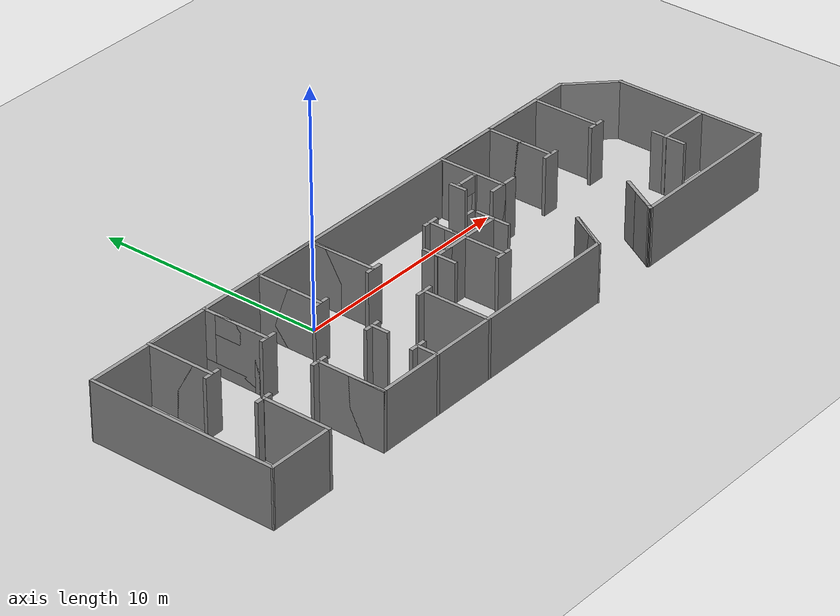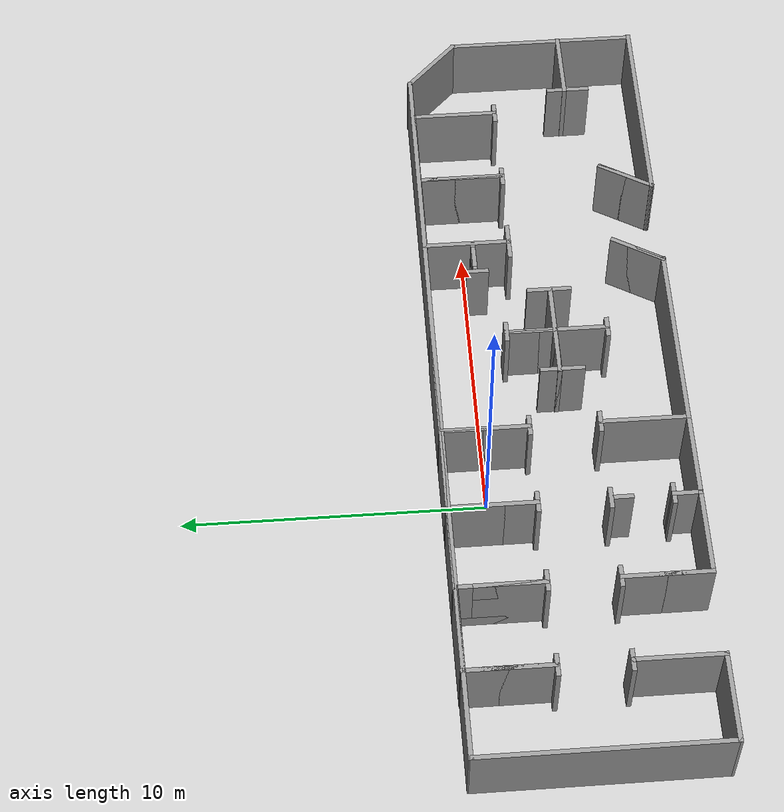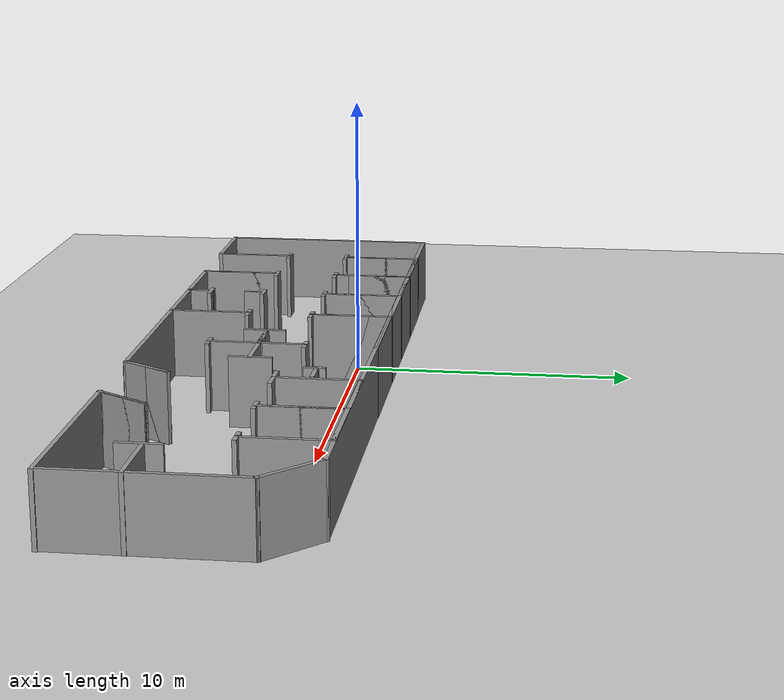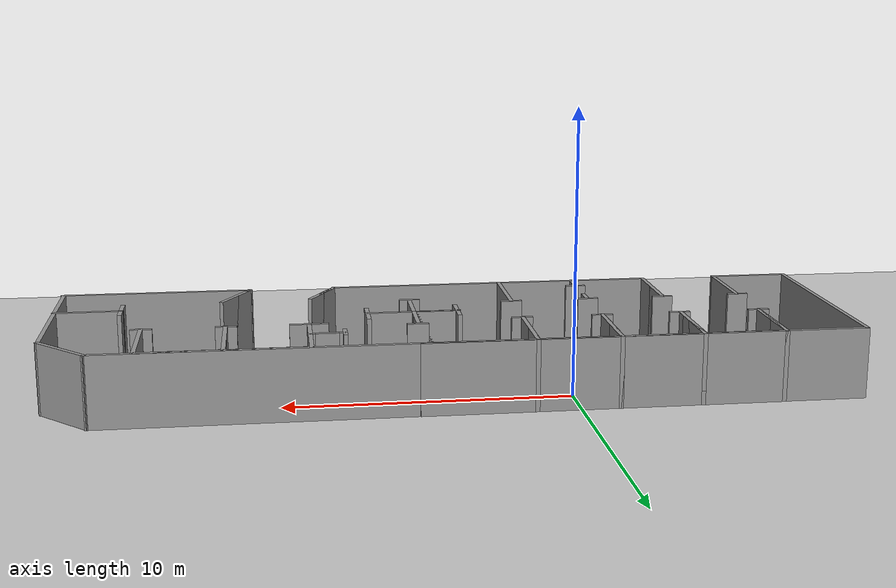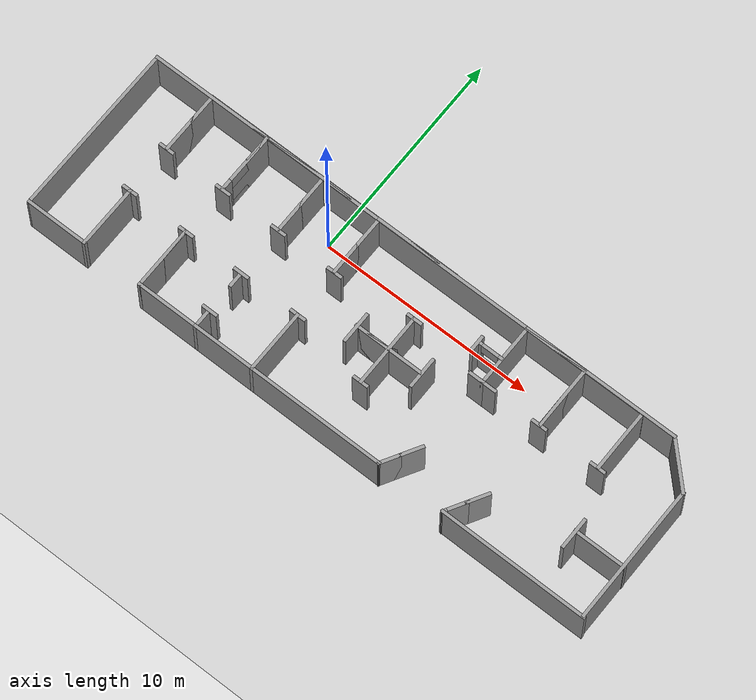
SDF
<sdf version="1.7">
 <world name="default">
  <model name="ground_plane">
   <static>1</static>
   <link name="link">
    <collision name="collision">
     <geometry><plane><normal>0 0 1</normal><size>100 100</size></plane></geometry>
     <surface>
      <contact><collide_bitmask>65535</collide_bitmask></contact>
      <friction><ode><mu>100</mu><mu2>50</mu2></ode></friction>
     </surface>
    </collision>
    <visual name="visual">
     <cast_shadows>0</cast_shadows>
     <geometry><plane><normal>0 0 1</normal><size>100 100</size></plane></geometry>
     <material>
      <script><uri>file://media/materials/scripts/gazebo.material</uri><name>Gazebo/Grey</name></script>
     </material>
    </visual>
   </link>
  </model>
  <light name="sun" type="directional">
   <pose>0 0 10 0 -0 0</pose>
   <diffuse>0.8 0.8 0.8 1</diffuse>
   <specular>0.2 0.2 0.2 1</specular>
   <attenuation>
    <range>1000</range>
    <constant>0.9</constant>
    <linear>0.01</linear>
    <quadratic>0.001</quadratic>
   </attenuation>
   <direction>-0.5 0.1 -0.9</direction>
   <spot><inner_angle>0</inner_angle><outer_angle>0</outer_angle><falloff>0</falloff></spot>
  </light>
  <gravity>0 0 -9.8</gravity>
  <magnetic_field>6e-06 2.3e-05 -4.2e-05</magnetic_field>
  <atmosphere type="adiabatic"/>
  <physics type="ode">
   <max_step_size>0.001</max_step_size>
   <real_time_factor>1</real_time_factor>
   <real_time_update_rate>1000</real_time_update_rate>
  </physics>
  <scene><ambient>0.4 0.4 0.4 1</ambient><background>0.7 0.7 0.7 1</background><shadows>1</shadows></scene>
  <spherical_coordinates>
   <surface_model>EARTH_WGS84</surface_model>
   <latitude_deg>0</latitude_deg>
   <longitude_deg>0</longitude_deg>
   <elevation>0</elevation>
   <heading_deg>0</heading_deg>
  </spherical_coordinates>
  <model name="test_office_top">
   <link name="Wall_101">
    <pose>-2.48394 -1.15101 0 0 -0 0</pose>
    <visual name="Wall_101_Visual">
     <pose>0 0 1.25 0 -0 0</pose>
     <geometry><box><size>0.76749 0.15 2.5</size></box></geometry>
     <material>
      <script><uri>file://media/materials/scripts/gazebo.material</uri><name>Gazebo/Grey</name></script>
      <ambient>1 1 1 1</ambient>
      <shader type="pixel"/>
     </material>
     <meta><layer>0</layer></meta>
    </visual>
    <collision name="Wall_101_Collision">
     <pose>0 0 1.25 0 -0 0</pose>
     <geometry><box><size>0.76749 0.15 2.5</size></box></geometry>
     <surface>
      <friction>
       <ode><mu>1</mu><mu2>1</mu2><fdir1>0 0 0</fdir1><slip1>0</slip1><slip2>0</slip2></ode>
       <torsional>
        <coefficient>1</coefficient>
        <patch_radius>0</patch_radius>
        <surface_radius>0</surface_radius>
        <use_patch_radius>1</use_patch_radius>
        <ode><slip>0</slip></ode>
       </torsional>
      </friction>
      <bounce><restitution_coefficient>0</restitution_coefficient><threshold>1e+06</threshold></bounce>
      <contact>
       <collide_without_contact>0</collide_without_contact>
       <collide_without_contact_bitmask>1</collide_without_contact_bitmask>
       <collide_bitmask>1</collide_bitmask>
       <ode>
        <soft_cfm>0</soft_cfm>
        <soft_erp>0.2</soft_erp>
        <kp>1e+13</kp>
        <kd>1</kd>
        <max_vel>0.01</max_vel>
        <min_depth>0</min_depth>
       </ode>
       <bullet>
        <split_impulse>1</split_impulse>
        <split_impulse_penetration_threshold>-0.01</split_impulse_penetration_threshold>
        <soft_cfm>0</soft_cfm>
        <soft_erp>0.2</soft_erp>
        <kp>1e+13</kp>
        <kd>1</kd>
       </bullet>
      </contact>
     </surface>
    </collision>
   </link>
   <link name="Wall_103">
    <pose>-2.4752 1.15727 0 0 -0 0</pose>
    <visual name="Wall_103_Visual">
     <pose>0 0 1.25 0 -0 0</pose>
     <geometry><box><size>0.75 0.15 2.5</size></box></geometry>
     <material>
      <script><uri>file://media/materials/scripts/gazebo.material</uri><name>Gazebo/Grey</name></script>
      <ambient>1 1 1 1</ambient>
      <shader type="pixel"/>
     </material>
     <meta><layer>0</layer></meta>
    </visual>
    <collision name="Wall_103_Collision">
     <pose>0 0 1.25 0 -0 0</pose>
     <geometry><box><size>0.75 0.15 2.5</size></box></geometry>
     <surface>
      <friction>
       <ode><mu>1</mu><mu2>1</mu2><fdir1>0 0 0</fdir1><slip1>0</slip1><slip2>0</slip2></ode>
       <torsional>
        <coefficient>1</coefficient>
        <patch_radius>0</patch_radius>
        <surface_radius>0</surface_radius>
        <use_patch_radius>1</use_patch_radius>
        <ode><slip>0</slip></ode>
       </torsional>
      </friction>
      <bounce><restitution_coefficient>0</restitution_coefficient><threshold>1e+06</threshold></bounce>
      <contact>
       <collide_without_contact>0</collide_without_contact>
       <collide_without_contact_bitmask>1</collide_without_contact_bitmask>
       <collide_bitmask>1</collide_bitmask>
       <ode>
        <soft_cfm>0</soft_cfm>
        <soft_erp>0.2</soft_erp>
        <kp>1e+13</kp>
        <kd>1</kd>
        <max_vel>0.01</max_vel>
        <min_depth>0</min_depth>
       </ode>
       <bullet>
        <split_impulse>1</split_impulse>
        <split_impulse_penetration_threshold>-0.01</split_impulse_penetration_threshold>
        <soft_cfm>0</soft_cfm>
        <soft_erp>0.2</soft_erp>
        <kp>1e+13</kp>
        <kd>1</kd>
       </bullet>
      </contact>
     </surface>
    </collision>
   </link>
   <link name="Wall_11">
    <pose>-11.0535 2.61067 0 0 0 -1.5708</pose>
    <visual name="Wall_11_Visual">
     <pose>0 0 1.25 0 -0 0</pose>
     <geometry><box><size>3 0.15 2.5</size></box></geometry>
     <material>
      <script><uri>file://media/materials/scripts/gazebo.material</uri><name>Gazebo/Grey</name></script>
      <ambient>1 1 1 1</ambient>
      <shader type="pixel"/>
     </material>
     <meta><layer>0</layer></meta>
    </visual>
    <collision name="Wall_11_Collision">
     <pose>0 0 1.25 0 -0 0</pose>
     <geometry><box><size>3 0.15 2.5</size></box></geometry>
     <surface>
      <friction>
       <ode><mu>1</mu><mu2>1</mu2><fdir1>0 0 0</fdir1><slip1>0</slip1><slip2>0</slip2></ode>
       <torsional>
        <coefficient>1</coefficient>
        <patch_radius>0</patch_radius>
        <surface_radius>0</surface_radius>
        <use_patch_radius>1</use_patch_radius>
        <ode><slip>0</slip></ode>
       </torsional>
      </friction>
      <bounce><restitution_coefficient>0</restitution_coefficient><threshold>1e+06</threshold></bounce>
      <contact>
       <collide_without_contact>0</collide_without_contact>
       <collide_without_contact_bitmask>1</collide_without_contact_bitmask>
       <collide_bitmask>1</collide_bitmask>
       <ode>
        <soft_cfm>0</soft_cfm>
        <soft_erp>0.2</soft_erp>
        <kp>1e+13</kp>
        <kd>1</kd>
        <max_vel>0.01</max_vel>
        <min_depth>0</min_depth>
       </ode>
       <bullet>
        <split_impulse>1</split_impulse>
        <split_impulse_penetration_threshold>-0.01</split_impulse_penetration_threshold>
        <soft_cfm>0</soft_cfm>
        <soft_erp>0.2</soft_erp>
        <kp>1e+13</kp>
        <kd>1</kd>
       </bullet>
      </contact>
     </surface>
    </collision>
   </link>
   <link name="Wall_12">
    <pose>-11.0535 2.61067 0 0 -0 1.5708</pose>
    <visual name="Wall_12_Visual">
     <pose>0 0 1.25 0 -0 0</pose>
     <geometry><box><size>3 0.15 2.5</size></box></geometry>
     <material>
      <script><uri>file://media/materials/scripts/gazebo.material</uri><name>Gazebo/Grey</name></script>
      <ambient>1 1 1 1</ambient>
      <shader type="pixel"/>
     </material>
     <meta><layer>0</layer></meta>
    </visual>
    <collision name="Wall_12_Collision">
     <pose>0 0 1.25 0 -0 0</pose>
     <geometry><box><size>3 0.15 2.5</size></box></geometry>
     <surface>
      <friction>
       <ode><mu>1</mu><mu2>1</mu2><fdir1>0 0 0</fdir1><slip1>0</slip1><slip2>0</slip2></ode>
       <torsional>
        <coefficient>1</coefficient>
        <patch_radius>0</patch_radius>
        <surface_radius>0</surface_radius>
        <use_patch_radius>1</use_patch_radius>
        <ode><slip>0</slip></ode>
       </torsional>
      </friction>
      <bounce><restitution_coefficient>0</restitution_coefficient><threshold>1e+06</threshold></bounce>
      <contact>
       <collide_without_contact>0</collide_without_contact>
       <collide_without_contact_bitmask>1</collide_without_contact_bitmask>
       <collide_bitmask>1</collide_bitmask>
       <ode>
        <soft_cfm>0</soft_cfm>
        <soft_erp>0.2</soft_erp>
        <kp>1e+13</kp>
        <kd>1</kd>
        <max_vel>0.01</max_vel>
        <min_depth>0</min_depth>
       </ode>
       <bullet>
        <split_impulse>1</split_impulse>
        <split_impulse_penetration_threshold>-0.01</split_impulse_penetration_threshold>
        <soft_cfm>0</soft_cfm>
        <soft_erp>0.2</soft_erp>
        <kp>1e+13</kp>
        <kd>1</kd>
       </bullet>
      </contact>
     </surface>
    </collision>
   </link>
   <link name="Wall_13">
    <pose>-9.62852 4.03566 0 0 -0 0</pose>
    <visual name="Wall_13_Visual">
     <pose>0 0 1.25 0 -0 0</pose>
     <geometry><box><size>3 0.15 2.5</size></box></geometry>
     <material>
      <script><uri>file://media/materials/scripts/gazebo.material</uri><name>Gazebo/Grey</name></script>
      <ambient>1 1 1 1</ambient>
      <shader type="pixel"/>
     </material>
     <meta><layer>0</layer></meta>
    </visual>
    <collision name="Wall_13_Collision">
     <pose>0 0 1.25 0 -0 0</pose>
     <geometry><box><size>3 0.15 2.5</size></box></geometry>
     <surface>
      <friction>
       <ode><mu>1</mu><mu2>1</mu2><fdir1>0 0 0</fdir1><slip1>0</slip1><slip2>0</slip2></ode>
       <torsional>
        <coefficient>1</coefficient>
        <patch_radius>0</patch_radius>
        <surface_radius>0</surface_radius>
        <use_patch_radius>1</use_patch_radius>
        <ode><slip>0</slip></ode>
       </torsional>
      </friction>
      <bounce><restitution_coefficient>0</restitution_coefficient><threshold>1e+06</threshold></bounce>
      <contact>
       <collide_without_contact>0</collide_without_contact>
       <collide_without_contact_bitmask>1</collide_without_contact_bitmask>
       <collide_bitmask>1</collide_bitmask>
       <ode>
        <soft_cfm>0</soft_cfm>
        <soft_erp>0.2</soft_erp>
        <kp>1e+13</kp>
        <kd>1</kd>
        <max_vel>0.01</max_vel>
        <min_depth>0</min_depth>
       </ode>
       <bullet>
        <split_impulse>1</split_impulse>
        <split_impulse_penetration_threshold>-0.01</split_impulse_penetration_threshold>
        <soft_cfm>0</soft_cfm>
        <soft_erp>0.2</soft_erp>
        <kp>1e+13</kp>
        <kd>1</kd>
       </bullet>
      </contact>
     </surface>
    </collision>
   </link>
   <link name="Wall_14">
    <pose>-8.20352 2.61067 0 0 0 -1.5708</pose>
    <visual name="Wall_14_Visual">
     <pose>0 0 1.25 0 -0 0</pose>
     <geometry><box><size>3 0.15 2.5</size></box></geometry>
     <material>
      <script><uri>file://media/materials/scripts/gazebo.material</uri><name>Gazebo/Grey</name></script>
      <ambient>1 1 1 1</ambient>
      <shader type="pixel"/>
     </material>
     <meta><layer>0</layer></meta>
    </visual>
    <collision name="Wall_14_Collision">
     <pose>0 0 1.25 0 -0 0</pose>
     <geometry><box><size>3 0.15 2.5</size></box></geometry>
     <surface>
      <friction>
       <ode><mu>1</mu><mu2>1</mu2><fdir1>0 0 0</fdir1><slip1>0</slip1><slip2>0</slip2></ode>
       <torsional>
        <coefficient>1</coefficient>
        <patch_radius>0</patch_radius>
        <surface_radius>0</surface_radius>
        <use_patch_radius>1</use_patch_radius>
        <ode><slip>0</slip></ode>
       </torsional>
      </friction>
      <bounce><restitution_coefficient>0</restitution_coefficient><threshold>1e+06</threshold></bounce>
      <contact>
       <collide_without_contact>0</collide_without_contact>
       <collide_without_contact_bitmask>1</collide_without_contact_bitmask>
       <collide_bitmask>1</collide_bitmask>
       <ode>
        <soft_cfm>0</soft_cfm>
        <soft_erp>0.2</soft_erp>
        <kp>1e+13</kp>
        <kd>1</kd>
        <max_vel>0.01</max_vel>
        <min_depth>0</min_depth>
       </ode>
       <bullet>
        <split_impulse>1</split_impulse>
        <split_impulse_penetration_threshold>-0.01</split_impulse_penetration_threshold>
        <soft_cfm>0</soft_cfm>
        <soft_erp>0.2</soft_erp>
        <kp>1e+13</kp>
        <kd>1</kd>
       </bullet>
      </contact>
     </surface>
    </collision>
   </link>
   <link name="Wall_15">
    <pose>-8.20352 2.61067 0 0 -0 1.5708</pose>
    <visual name="Wall_15_Visual_0">
     <pose>-1.21259 0 1.25 0 -0 0</pose>
     <geometry><box><size>0.574817 0.15 2.5</size></box></geometry>
     <material>
      <script><uri>file://media/materials/scripts/gazebo.material</uri><name>Gazebo/Grey</name></script>
      <ambient>1 1 1 1</ambient>
      <shader type="pixel"/>
     </material>
     <meta><layer>0</layer></meta>
    </visual>
    <visual name="Wall_15_Visual_1">
     <pose>0.287408 0 0.25 0 -0 0</pose>
     <geometry><box><size>2.42518 0.15 0.5</size></box></geometry>
     <material>
      <script><uri>file://media/materials/scripts/gazebo.material</uri><name>Gazebo/Grey</name></script>
      <ambient>1 1 1 1</ambient>
      <shader type="pixel"/>
     </material>
     <meta><layer>0</layer></meta>
    </visual>
    <visual name="Wall_15_Visual_2">
     <pose>1.18741 0 1.5 0 -0 0</pose>
     <geometry><box><size>0.625183 0.15 2</size></box></geometry>
     <material>
      <script><uri>file://media/materials/scripts/gazebo.material</uri><name>Gazebo/Grey</name></script>
      <ambient>1 1 1 1</ambient>
      <shader type="pixel"/>
     </material>
     <meta><layer>0</layer></meta>
    </visual>
    <visual name="Wall_15_Visual_3">
     <pose>-0.025183 0 2.1 0 -0 0</pose>
     <geometry><box><size>1.8 0.15 0.8</size></box></geometry>
     <material>
      <script><uri>file://media/materials/scripts/gazebo.material</uri><name>Gazebo/Grey</name></script>
      <ambient>1 1 1 1</ambient>
      <shader type="pixel"/>
     </material>
     <meta><layer>0</layer></meta>
    </visual>
    <collision name="Wall_15_Collision_3">
     <pose>-0.025183 0 2.1 0 -0 0</pose>
     <geometry><box><size>1.8 0.15 0.8</size></box></geometry>
     <surface>
      <friction>
       <ode><mu>1</mu><mu2>1</mu2><fdir1>0 0 0</fdir1><slip1>0</slip1><slip2>0</slip2></ode>
       <torsional>
        <coefficient>1</coefficient>
        <patch_radius>0</patch_radius>
        <surface_radius>0</surface_radius>
        <use_patch_radius>1</use_patch_radius>
        <ode><slip>0</slip></ode>
       </torsional>
      </friction>
      <bounce><restitution_coefficient>0</restitution_coefficient><threshold>1e+06</threshold></bounce>
      <contact>
       <collide_without_contact>0</collide_without_contact>
       <collide_without_contact_bitmask>1</collide_without_contact_bitmask>
       <collide_bitmask>1</collide_bitmask>
       <ode>
        <soft_cfm>0</soft_cfm>
        <soft_erp>0.2</soft_erp>
        <kp>1e+13</kp>
        <kd>1</kd>
        <max_vel>0.01</max_vel>
        <min_depth>0</min_depth>
       </ode>
       <bullet>
        <split_impulse>1</split_impulse>
        <split_impulse_penetration_threshold>-0.01</split_impulse_penetration_threshold>
        <soft_cfm>0</soft_cfm>
        <soft_erp>0.2</soft_erp>
        <kp>1e+13</kp>
        <kd>1</kd>
       </bullet>
      </contact>
     </surface>
    </collision>
    <collision name="Wall_15_Collision_0">
     <pose>-1.21259 0 1.25 0 -0 0</pose>
     <geometry><box><size>0.574817 0.15 2.5</size></box></geometry>
     <surface>
      <friction>
       <ode><mu>1</mu><mu2>1</mu2><fdir1>0 0 0</fdir1><slip1>0</slip1><slip2>0</slip2></ode>
       <torsional>
        <coefficient>1</coefficient>
        <patch_radius>0</patch_radius>
        <surface_radius>0</surface_radius>
        <use_patch_radius>1</use_patch_radius>
        <ode><slip>0</slip></ode>
       </torsional>
      </friction>
      <bounce><restitution_coefficient>0</restitution_coefficient><threshold>1e+06</threshold></bounce>
      <contact>
       <collide_without_contact>0</collide_without_contact>
       <collide_without_contact_bitmask>1</collide_without_contact_bitmask>
       <collide_bitmask>1</collide_bitmask>
       <ode>
        <soft_cfm>0</soft_cfm>
        <soft_erp>0.2</soft_erp>
        <kp>1e+13</kp>
        <kd>1</kd>
        <max_vel>0.01</max_vel>
        <min_depth>0</min_depth>
       </ode>
       <bullet>
        <split_impulse>1</split_impulse>
        <split_impulse_penetration_threshold>-0.01</split_impulse_penetration_threshold>
        <soft_cfm>0</soft_cfm>
        <soft_erp>0.2</soft_erp>
        <kp>1e+13</kp>
        <kd>1</kd>
       </bullet>
      </contact>
     </surface>
    </collision>
    <collision name="Wall_15_Collision_1">
     <pose>0.287408 0 0.25 0 -0 0</pose>
     <geometry><box><size>2.42518 0.15 0.5</size></box></geometry>
     <surface>
      <friction>
       <ode><mu>1</mu><mu2>1</mu2><fdir1>0 0 0</fdir1><slip1>0</slip1><slip2>0</slip2></ode>
       <torsional>
        <coefficient>1</coefficient>
        <patch_radius>0</patch_radius>
        <surface_radius>0</surface_radius>
        <use_patch_radius>1</use_patch_radius>
        <ode><slip>0</slip></ode>
       </torsional>
      </friction>
      <bounce><restitution_coefficient>0</restitution_coefficient><threshold>1e+06</threshold></bounce>
      <contact>
       <collide_without_contact>0</collide_without_contact>
       <collide_without_contact_bitmask>1</collide_without_contact_bitmask>
       <collide_bitmask>1</collide_bitmask>
       <ode>
        <soft_cfm>0</soft_cfm>
        <soft_erp>0.2</soft_erp>
        <kp>1e+13</kp>
        <kd>1</kd>
        <max_vel>0.01</max_vel>
        <min_depth>0</min_depth>
       </ode>
       <bullet>
        <split_impulse>1</split_impulse>
        <split_impulse_penetration_threshold>-0.01</split_impulse_penetration_threshold>
        <soft_cfm>0</soft_cfm>
        <soft_erp>0.2</soft_erp>
        <kp>1e+13</kp>
        <kd>1</kd>
       </bullet>
      </contact>
     </surface>
    </collision>
    <collision name="Wall_15_Collision_2">
     <pose>1.18741 0 1.5 0 -0 0</pose>
     <geometry><box><size>0.625183 0.15 2</size></box></geometry>
     <surface>
      <friction>
       <ode><mu>1</mu><mu2>1</mu2><fdir1>0 0 0</fdir1><slip1>0</slip1><slip2>0</slip2></ode>
       <torsional>
        <coefficient>1</coefficient>
        <patch_radius>0</patch_radius>
        <surface_radius>0</surface_radius>
        <use_patch_radius>1</use_patch_radius>
        <ode><slip>0</slip></ode>
       </torsional>
      </friction>
      <bounce><restitution_coefficient>0</restitution_coefficient><threshold>1e+06</threshold></bounce>
      <contact>
       <collide_without_contact>0</collide_without_contact>
       <collide_without_contact_bitmask>1</collide_without_contact_bitmask>
       <collide_bitmask>1</collide_bitmask>
       <ode>
        <soft_cfm>0</soft_cfm>
        <soft_erp>0.2</soft_erp>
        <kp>1e+13</kp>
        <kd>1</kd>
        <max_vel>0.01</max_vel>
        <min_depth>0</min_depth>
       </ode>
       <bullet>
        <split_impulse>1</split_impulse>
        <split_impulse_penetration_threshold>-0.01</split_impulse_penetration_threshold>
        <soft_cfm>0</soft_cfm>
        <soft_erp>0.2</soft_erp>
        <kp>1e+13</kp>
        <kd>1</kd>
       </bullet>
      </contact>
     </surface>
    </collision>
   </link>
   <link name="Wall_16">
    <pose>-6.77852 4.03566 0 0 -0 0</pose>
    <visual name="Wall_16_Visual">
     <pose>0 0 1.25 0 -0 0</pose>
     <geometry><box><size>3 0.15 2.5</size></box></geometry>
     <material>
      <script><uri>file://media/materials/scripts/gazebo.material</uri><name>Gazebo/Grey</name></script>
      <ambient>1 1 1 1</ambient>
      <shader type="pixel"/>
     </material>
     <meta><layer>0</layer></meta>
    </visual>
    <collision name="Wall_16_Collision">
     <pose>0 0 1.25 0 -0 0</pose>
     <geometry><box><size>3 0.15 2.5</size></box></geometry>
     <surface>
      <friction>
       <ode><mu>1</mu><mu2>1</mu2><fdir1>0 0 0</fdir1><slip1>0</slip1><slip2>0</slip2></ode>
       <torsional>
        <coefficient>1</coefficient>
        <patch_radius>0</patch_radius>
        <surface_radius>0</surface_radius>
        <use_patch_radius>1</use_patch_radius>
        <ode><slip>0</slip></ode>
       </torsional>
      </friction>
      <bounce><restitution_coefficient>0</restitution_coefficient><threshold>1e+06</threshold></bounce>
      <contact>
       <collide_without_contact>0</collide_without_contact>
       <collide_without_contact_bitmask>1</collide_without_contact_bitmask>
       <collide_bitmask>1</collide_bitmask>
       <ode>
        <soft_cfm>0</soft_cfm>
        <soft_erp>0.2</soft_erp>
        <kp>1e+13</kp>
        <kd>1</kd>
        <max_vel>0.01</max_vel>
        <min_depth>0</min_depth>
       </ode>
       <bullet>
        <split_impulse>1</split_impulse>
        <split_impulse_penetration_threshold>-0.01</split_impulse_penetration_threshold>
        <soft_cfm>0</soft_cfm>
        <soft_erp>0.2</soft_erp>
        <kp>1e+13</kp>
        <kd>1</kd>
       </bullet>
      </contact>
     </surface>
    </collision>
   </link>
   <link name="Wall_164">
    <pose>0.681479 -4.01433 0 0 -0 0</pose>
    <visual name="Wall_164_Visual">
     <pose>0 0 1.25 0 -0 0</pose>
     <geometry><box><size>6.5 0.15 2.5</size></box></geometry>
     <material>
      <script><uri>file://media/materials/scripts/gazebo.material</uri><name>Gazebo/Grey</name></script>
      <ambient>1 1 1 1</ambient>
      <shader type="pixel"/>
     </material>
     <meta><layer>0</layer></meta>
    </visual>
    <collision name="Wall_164_Collision">
     <pose>0 0 1.25 0 -0 0</pose>
     <geometry><box><size>6.5 0.15 2.5</size></box></geometry>
     <surface>
      <friction>
       <ode><mu>1</mu><mu2>1</mu2><fdir1>0 0 0</fdir1><slip1>0</slip1><slip2>0</slip2></ode>
       <torsional>
        <coefficient>1</coefficient>
        <patch_radius>0</patch_radius>
        <surface_radius>0</surface_radius>
        <use_patch_radius>1</use_patch_radius>
        <ode><slip>0</slip></ode>
       </torsional>
      </friction>
      <bounce><restitution_coefficient>0</restitution_coefficient><threshold>1e+06</threshold></bounce>
      <contact>
       <collide_without_contact>0</collide_without_contact>
       <collide_without_contact_bitmask>1</collide_without_contact_bitmask>
       <collide_bitmask>1</collide_bitmask>
       <ode>
        <soft_cfm>0</soft_cfm>
        <soft_erp>0.2</soft_erp>
        <kp>1e+13</kp>
        <kd>1</kd>
        <max_vel>0.01</max_vel>
        <min_depth>0</min_depth>
       </ode>
       <bullet>
        <split_impulse>1</split_impulse>
        <split_impulse_penetration_threshold>-0.01</split_impulse_penetration_threshold>
        <soft_cfm>0</soft_cfm>
        <soft_erp>0.2</soft_erp>
        <kp>1e+13</kp>
        <kd>1</kd>
       </bullet>
      </contact>
     </surface>
    </collision>
   </link>
   <link name="Wall_17">
    <pose>-5.35352 2.61067 0 0 0 -1.5708</pose>
    <visual name="Wall_17_Visual">
     <pose>0 0 1.25 0 -0 0</pose>
     <geometry><box><size>3 0.15 2.5</size></box></geometry>
     <material>
      <script><uri>file://media/materials/scripts/gazebo.material</uri><name>Gazebo/Grey</name></script>
      <ambient>1 1 1 1</ambient>
      <shader type="pixel"/>
     </material>
     <meta><layer>0</layer></meta>
    </visual>
    <collision name="Wall_17_Collision">
     <pose>0 0 1.25 0 -0 0</pose>
     <geometry><box><size>3 0.15 2.5</size></box></geometry>
     <surface>
      <friction>
       <ode><mu>1</mu><mu2>1</mu2><fdir1>0 0 0</fdir1><slip1>0</slip1><slip2>0</slip2></ode>
       <torsional>
        <coefficient>1</coefficient>
        <patch_radius>0</patch_radius>
        <surface_radius>0</surface_radius>
        <use_patch_radius>1</use_patch_radius>
        <ode><slip>0</slip></ode>
       </torsional>
      </friction>
      <bounce><restitution_coefficient>0</restitution_coefficient><threshold>1e+06</threshold></bounce>
      <contact>
       <collide_without_contact>0</collide_without_contact>
       <collide_without_contact_bitmask>1</collide_without_contact_bitmask>
       <collide_bitmask>1</collide_bitmask>
       <ode>
        <soft_cfm>0</soft_cfm>
        <soft_erp>0.2</soft_erp>
        <kp>1e+13</kp>
        <kd>1</kd>
        <max_vel>0.01</max_vel>
        <min_depth>0</min_depth>
       </ode>
       <bullet>
        <split_impulse>1</split_impulse>
        <split_impulse_penetration_threshold>-0.01</split_impulse_penetration_threshold>
        <soft_cfm>0</soft_cfm>
        <soft_erp>0.2</soft_erp>
        <kp>1e+13</kp>
        <kd>1</kd>
       </bullet>
      </contact>
     </surface>
    </collision>
   </link>
   <link name="Wall_170">
    <pose>-3.91852 -4.01433 0 0 -0 0</pose>
    <visual name="Wall_170_Visual">
     <pose>0 0 1.25 0 -0 0</pose>
     <geometry><box><size>3 0.15 2.5</size></box></geometry>
     <material>
      <script><uri>file://media/materials/scripts/gazebo.material</uri><name>Gazebo/Grey</name></script>
      <ambient>1 1 1 1</ambient>
      <shader type="pixel"/>
     </material>
     <meta><layer>0</layer></meta>
    </visual>
    <collision name="Wall_170_Collision">
     <pose>0 0 1.25 0 -0 0</pose>
     <geometry><box><size>3 0.15 2.5</size></box></geometry>
     <surface>
      <friction>
       <ode><mu>1</mu><mu2>1</mu2><fdir1>0 0 0</fdir1><slip1>0</slip1><slip2>0</slip2></ode>
       <torsional>
        <coefficient>1</coefficient>
        <patch_radius>0</patch_radius>
        <surface_radius>0</surface_radius>
        <use_patch_radius>1</use_patch_radius>
        <ode><slip>0</slip></ode>
       </torsional>
      </friction>
      <bounce><restitution_coefficient>0</restitution_coefficient><threshold>1e+06</threshold></bounce>
      <contact>
       <collide_without_contact>0</collide_without_contact>
       <collide_without_contact_bitmask>1</collide_without_contact_bitmask>
       <collide_bitmask>1</collide_bitmask>
       <ode>
        <soft_cfm>0</soft_cfm>
        <soft_erp>0.2</soft_erp>
        <kp>1e+13</kp>
        <kd>1</kd>
        <max_vel>0.01</max_vel>
        <min_depth>0</min_depth>
       </ode>
       <bullet>
        <split_impulse>1</split_impulse>
        <split_impulse_penetration_threshold>-0.01</split_impulse_penetration_threshold>
        <soft_cfm>0</soft_cfm>
        <soft_erp>0.2</soft_erp>
        <kp>1e+13</kp>
        <kd>1</kd>
       </bullet>
      </contact>
     </surface>
    </collision>
   </link>
   <link name="Wall_172">
    <pose>4.31898 -3.21326 0 0 -0 1.0472</pose>
    <visual name="Wall_172_Visual">
     <pose>0 0 1.25 0 -0 0</pose>
     <geometry><box><size>2 0.15 2.5</size></box></geometry>
     <material>
      <script><uri>file://media/materials/scripts/gazebo.material</uri><name>Gazebo/Grey</name></script>
      <ambient>1 1 1 1</ambient>
      <shader type="pixel"/>
     </material>
     <meta><layer>0</layer></meta>
    </visual>
    <collision name="Wall_172_Collision">
     <pose>0 0 1.25 0 -0 0</pose>
     <geometry><box><size>2 0.15 2.5</size></box></geometry>
     <surface>
      <friction>
       <ode><mu>1</mu><mu2>1</mu2><fdir1>0 0 0</fdir1><slip1>0</slip1><slip2>0</slip2></ode>
       <torsional>
        <coefficient>1</coefficient>
        <patch_radius>0</patch_radius>
        <surface_radius>0</surface_radius>
        <use_patch_radius>1</use_patch_radius>
        <ode><slip>0</slip></ode>
       </torsional>
      </friction>
      <bounce><restitution_coefficient>0</restitution_coefficient><threshold>1e+06</threshold></bounce>
      <contact>
       <collide_without_contact>0</collide_without_contact>
       <collide_without_contact_bitmask>1</collide_without_contact_bitmask>
       <collide_bitmask>1</collide_bitmask>
       <ode>
        <soft_cfm>0</soft_cfm>
        <soft_erp>0.2</soft_erp>
        <kp>1e+13</kp>
        <kd>1</kd>
        <max_vel>0.01</max_vel>
        <min_depth>0</min_depth>
       </ode>
       <bullet>
        <split_impulse>1</split_impulse>
        <split_impulse_penetration_threshold>-0.01</split_impulse_penetration_threshold>
        <soft_cfm>0</soft_cfm>
        <soft_erp>0.2</soft_erp>
        <kp>1e+13</kp>
        <kd>1</kd>
       </bullet>
      </contact>
     </surface>
    </collision>
   </link>
   <link name="Wall_173">
    <pose>4.31898 -3.21326 0 0 0 -2.0944</pose>
    <visual name="Wall_173_Visual">
     <pose>0 0 1.25 0 -0 0</pose>
     <geometry><box><size>2 0.15 2.5</size></box></geometry>
     <material>
      <script><uri>file://media/materials/scripts/gazebo.material</uri><name>Gazebo/Grey</name></script>
      <ambient>1 1 1 1</ambient>
      <shader type="pixel"/>
     </material>
     <meta><layer>0</layer></meta>
    </visual>
    <collision name="Wall_173_Collision">
     <pose>0 0 1.25 0 -0 0</pose>
     <geometry><box><size>2 0.15 2.5</size></box></geometry>
     <surface>
      <friction>
       <ode><mu>1</mu><mu2>1</mu2><fdir1>0 0 0</fdir1><slip1>0</slip1><slip2>0</slip2></ode>
       <torsional>
        <coefficient>1</coefficient>
        <patch_radius>0</patch_radius>
        <surface_radius>0</surface_radius>
        <use_patch_radius>1</use_patch_radius>
        <ode><slip>0</slip></ode>
       </torsional>
      </friction>
      <bounce><restitution_coefficient>0</restitution_coefficient><threshold>1e+06</threshold></bounce>
      <contact>
       <collide_without_contact>0</collide_without_contact>
       <collide_without_contact_bitmask>1</collide_without_contact_bitmask>
       <collide_bitmask>1</collide_bitmask>
       <ode>
        <soft_cfm>0</soft_cfm>
        <soft_erp>0.2</soft_erp>
        <kp>1e+13</kp>
        <kd>1</kd>
        <max_vel>0.01</max_vel>
        <min_depth>0</min_depth>
       </ode>
       <bullet>
        <split_impulse>1</split_impulse>
        <split_impulse_penetration_threshold>-0.01</split_impulse_penetration_threshold>
        <soft_cfm>0</soft_cfm>
        <soft_erp>0.2</soft_erp>
        <kp>1e+13</kp>
        <kd>1</kd>
       </bullet>
      </contact>
     </surface>
    </collision>
   </link>
   <link name="Wall_18">
    <pose>-5.35352 2.61067 0 0 -0 1.5708</pose>
    <visual name="Wall_18_Visual">
     <pose>0 0 1.25 0 -0 0</pose>
     <geometry><box><size>3 0.15 2.5</size></box></geometry>
     <material>
      <script><uri>file://media/materials/scripts/gazebo.material</uri><name>Gazebo/Grey</name></script>
      <ambient>1 1 1 1</ambient>
      <shader type="pixel"/>
     </material>
     <meta><layer>0</layer></meta>
    </visual>
    <collision name="Wall_18_Collision">
     <pose>0 0 1.25 0 -0 0</pose>
     <geometry><box><size>3 0.15 2.5</size></box></geometry>
     <surface>
      <friction>
       <ode><mu>1</mu><mu2>1</mu2><fdir1>0 0 0</fdir1><slip1>0</slip1><slip2>0</slip2></ode>
       <torsional>
        <coefficient>1</coefficient>
        <patch_radius>0</patch_radius>
        <surface_radius>0</surface_radius>
        <use_patch_radius>1</use_patch_radius>
        <ode><slip>0</slip></ode>
       </torsional>
      </friction>
      <bounce><restitution_coefficient>0</restitution_coefficient><threshold>1e+06</threshold></bounce>
      <contact>
       <collide_without_contact>0</collide_without_contact>
       <collide_without_contact_bitmask>1</collide_without_contact_bitmask>
       <collide_bitmask>1</collide_bitmask>
       <ode>
        <soft_cfm>0</soft_cfm>
        <soft_erp>0.2</soft_erp>
        <kp>1e+13</kp>
        <kd>1</kd>
        <max_vel>0.01</max_vel>
        <min_depth>0</min_depth>
       </ode>
       <bullet>
        <split_impulse>1</split_impulse>
        <split_impulse_penetration_threshold>-0.01</split_impulse_penetration_threshold>
        <soft_cfm>0</soft_cfm>
        <soft_erp>0.2</soft_erp>
        <kp>1e+13</kp>
        <kd>1</kd>
       </bullet>
      </contact>
     </surface>
    </collision>
   </link>
   <link name="Wall_19">
    <pose>-3.92852 4.03566 0 0 -0 0</pose>
    <visual name="Wall_19_Visual">
     <pose>0 0 1.25 0 -0 0</pose>
     <geometry><box><size>3 0.15 2.5</size></box></geometry>
     <material>
      <script><uri>file://media/materials/scripts/gazebo.material</uri><name>Gazebo/Grey</name></script>
      <ambient>1 1 1 1</ambient>
      <shader type="pixel"/>
     </material>
     <meta><layer>0</layer></meta>
    </visual>
    <collision name="Wall_19_Collision">
     <pose>0 0 1.25 0 -0 0</pose>
     <geometry><box><size>3 0.15 2.5</size></box></geometry>
     <surface>
      <friction>
       <ode><mu>1</mu><mu2>1</mu2><fdir1>0 0 0</fdir1><slip1>0</slip1><slip2>0</slip2></ode>
       <torsional>
        <coefficient>1</coefficient>
        <patch_radius>0</patch_radius>
        <surface_radius>0</surface_radius>
        <use_patch_radius>1</use_patch_radius>
        <ode><slip>0</slip></ode>
       </torsional>
      </friction>
      <bounce><restitution_coefficient>0</restitution_coefficient><threshold>1e+06</threshold></bounce>
      <contact>
       <collide_without_contact>0</collide_without_contact>
       <collide_without_contact_bitmask>1</collide_without_contact_bitmask>
       <collide_bitmask>1</collide_bitmask>
       <ode>
        <soft_cfm>0</soft_cfm>
        <soft_erp>0.2</soft_erp>
        <kp>1e+13</kp>
        <kd>1</kd>
        <max_vel>0.01</max_vel>
        <min_depth>0</min_depth>
       </ode>
       <bullet>
        <split_impulse>1</split_impulse>
        <split_impulse_penetration_threshold>-0.01</split_impulse_penetration_threshold>
        <soft_cfm>0</soft_cfm>
        <soft_erp>0.2</soft_erp>
        <kp>1e+13</kp>
        <kd>1</kd>
       </bullet>
      </contact>
     </surface>
    </collision>
   </link>
   <link name="Wall_196">
    <pose>7.53536 -3.13578 0 0 -0 1.0472</pose>
    <visual name="Wall_196_Visual">
     <pose>0 0 1.25 0 -0 0</pose>
     <geometry><box><size>2 0.15 2.5</size></box></geometry>
     <material>
      <script><uri>file://media/materials/scripts/gazebo.material</uri><name>Gazebo/Grey</name></script>
      <ambient>1 1 1 1</ambient>
      <shader type="pixel"/>
     </material>
     <meta><layer>0</layer></meta>
    </visual>
    <collision name="Wall_196_Collision">
     <pose>0 0 1.25 0 -0 0</pose>
     <geometry><box><size>2 0.15 2.5</size></box></geometry>
     <surface>
      <friction>
       <ode><mu>1</mu><mu2>1</mu2><fdir1>0 0 0</fdir1><slip1>0</slip1><slip2>0</slip2></ode>
       <torsional>
        <coefficient>1</coefficient>
        <patch_radius>0</patch_radius>
        <surface_radius>0</surface_radius>
        <use_patch_radius>1</use_patch_radius>
        <ode><slip>0</slip></ode>
       </torsional>
      </friction>
      <bounce><restitution_coefficient>0</restitution_coefficient><threshold>1e+06</threshold></bounce>
      <contact>
       <collide_without_contact>0</collide_without_contact>
       <collide_without_contact_bitmask>1</collide_without_contact_bitmask>
       <collide_bitmask>1</collide_bitmask>
       <ode>
        <soft_cfm>0</soft_cfm>
        <soft_erp>0.2</soft_erp>
        <kp>1e+13</kp>
        <kd>1</kd>
        <max_vel>0.01</max_vel>
        <min_depth>0</min_depth>
       </ode>
       <bullet>
        <split_impulse>1</split_impulse>
        <split_impulse_penetration_threshold>-0.01</split_impulse_penetration_threshold>
        <soft_cfm>0</soft_cfm>
        <soft_erp>0.2</soft_erp>
        <kp>1e+13</kp>
        <kd>1</kd>
       </bullet>
      </contact>
     </surface>
    </collision>
   </link>
   <link name="Wall_197">
    <pose>7.53536 -3.13578 0 0 0 -2.0944</pose>
    <visual name="Wall_197_Visual">
     <pose>0 0 1.25 0 -0 0</pose>
     <geometry><box><size>2 0.15 2.5</size></box></geometry>
     <material>
      <script><uri>file://media/materials/scripts/gazebo.material</uri><name>Gazebo/Grey</name></script>
      <ambient>1 1 1 1</ambient>
      <shader type="pixel"/>
     </material>
     <meta><layer>0</layer></meta>
    </visual>
    <collision name="Wall_197_Collision">
     <pose>0 0 1.25 0 -0 0</pose>
     <geometry><box><size>2 0.15 2.5</size></box></geometry>
     <surface>
      <friction>
       <ode><mu>1</mu><mu2>1</mu2><fdir1>0 0 0</fdir1><slip1>0</slip1><slip2>0</slip2></ode>
       <torsional>
        <coefficient>1</coefficient>
        <patch_radius>0</patch_radius>
        <surface_radius>0</surface_radius>
        <use_patch_radius>1</use_patch_radius>
        <ode><slip>0</slip></ode>
       </torsional>
      </friction>
      <bounce><restitution_coefficient>0</restitution_coefficient><threshold>1e+06</threshold></bounce>
      <contact>
       <collide_without_contact>0</collide_without_contact>
       <collide_without_contact_bitmask>1</collide_without_contact_bitmask>
       <collide_bitmask>1</collide_bitmask>
       <ode>
        <soft_cfm>0</soft_cfm>
        <soft_erp>0.2</soft_erp>
        <kp>1e+13</kp>
        <kd>1</kd>
        <max_vel>0.01</max_vel>
        <min_depth>0</min_depth>
       </ode>
       <bullet>
        <split_impulse>1</split_impulse>
        <split_impulse_penetration_threshold>-0.01</split_impulse_penetration_threshold>
        <soft_cfm>0</soft_cfm>
        <soft_erp>0.2</soft_erp>
        <kp>1e+13</kp>
        <kd>1</kd>
       </bullet>
      </contact>
     </surface>
    </collision>
   </link>
   <link name="Wall_198">
    <pose>7.04786 -3.98016 0 0 0 -2.0944</pose>
    <visual name="Wall_198_Visual">
     <pose>0 0 1.25 0 -0 0</pose>
     <geometry><box><size>0.25 0.15 2.5</size></box></geometry>
     <material>
      <script><uri>file://media/materials/scripts/gazebo.material</uri><name>Gazebo/Grey</name></script>
      <ambient>1 1 1 1</ambient>
      <shader type="pixel"/>
     </material>
     <meta><layer>0</layer></meta>
    </visual>
    <collision name="Wall_198_Collision">
     <pose>0 0 1.25 0 -0 0</pose>
     <geometry><box><size>0.25 0.15 2.5</size></box></geometry>
     <surface>
      <friction>
       <ode><mu>1</mu><mu2>1</mu2><fdir1>0 0 0</fdir1><slip1>0</slip1><slip2>0</slip2></ode>
       <torsional>
        <coefficient>1</coefficient>
        <patch_radius>0</patch_radius>
        <surface_radius>0</surface_radius>
        <use_patch_radius>1</use_patch_radius>
        <ode><slip>0</slip></ode>
       </torsional>
      </friction>
      <bounce><restitution_coefficient>0</restitution_coefficient><threshold>1e+06</threshold></bounce>
      <contact>
       <collide_without_contact>0</collide_without_contact>
       <collide_without_contact_bitmask>1</collide_without_contact_bitmask>
       <collide_bitmask>1</collide_bitmask>
       <ode>
        <soft_cfm>0</soft_cfm>
        <soft_erp>0.2</soft_erp>
        <kp>1e+13</kp>
        <kd>1</kd>
        <max_vel>0.01</max_vel>
        <min_depth>0</min_depth>
       </ode>
       <bullet>
        <split_impulse>1</split_impulse>
        <split_impulse_penetration_threshold>-0.01</split_impulse_penetration_threshold>
        <soft_cfm>0</soft_cfm>
        <soft_erp>0.2</soft_erp>
        <kp>1e+13</kp>
        <kd>1</kd>
       </bullet>
      </contact>
     </surface>
    </collision>
   </link>
   <link name="Wall_199">
    <pose>10.4632 -4.03111 0 0 0 -0.002223</pose>
    <visual name="Wall_199_Visual">
     <pose>0 0 1.25 0 -0 0</pose>
     <geometry><box><size>7.03061 0.15 2.5</size></box></geometry>
     <material>
      <script><uri>file://media/materials/scripts/gazebo.material</uri><name>Gazebo/Grey</name></script>
      <ambient>1 1 1 1</ambient>
      <shader type="pixel"/>
     </material>
     <meta><layer>0</layer></meta>
    </visual>
    <collision name="Wall_199_Collision">
     <pose>0 0 1.25 0 -0 0</pose>
     <geometry><box><size>7.03061 0.15 2.5</size></box></geometry>
     <surface>
      <friction>
       <ode><mu>1</mu><mu2>1</mu2><fdir1>0 0 0</fdir1><slip1>0</slip1><slip2>0</slip2></ode>
       <torsional>
        <coefficient>1</coefficient>
        <patch_radius>0</patch_radius>
        <surface_radius>0</surface_radius>
        <use_patch_radius>1</use_patch_radius>
        <ode><slip>0</slip></ode>
       </torsional>
      </friction>
      <bounce><restitution_coefficient>0</restitution_coefficient><threshold>1e+06</threshold></bounce>
      <contact>
       <collide_without_contact>0</collide_without_contact>
       <collide_without_contact_bitmask>1</collide_without_contact_bitmask>
       <collide_bitmask>1</collide_bitmask>
       <ode>
        <soft_cfm>0</soft_cfm>
        <soft_erp>0.2</soft_erp>
        <kp>1e+13</kp>
        <kd>1</kd>
        <max_vel>0.01</max_vel>
        <min_depth>0</min_depth>
       </ode>
       <bullet>
        <split_impulse>1</split_impulse>
        <split_impulse_penetration_threshold>-0.01</split_impulse_penetration_threshold>
        <soft_cfm>0</soft_cfm>
        <soft_erp>0.2</soft_erp>
        <kp>1e+13</kp>
        <kd>1</kd>
       </bullet>
      </contact>
     </surface>
    </collision>
   </link>
   <link name="Wall_20">
    <pose>-2.50352 2.61067 0 0 0 -1.5708</pose>
    <visual name="Wall_20_Visual">
     <pose>0 0 1.25 0 -0 0</pose>
     <geometry><box><size>3 0.15 2.5</size></box></geometry>
     <material>
      <script><uri>file://media/materials/scripts/gazebo.material</uri><name>Gazebo/Grey</name></script>
      <ambient>1 1 1 1</ambient>
      <shader type="pixel"/>
     </material>
     <meta><layer>0</layer></meta>
    </visual>
    <collision name="Wall_20_Collision">
     <pose>0 0 1.25 0 -0 0</pose>
     <geometry><box><size>3 0.15 2.5</size></box></geometry>
     <surface>
      <friction>
       <ode><mu>1</mu><mu2>1</mu2><fdir1>0 0 0</fdir1><slip1>0</slip1><slip2>0</slip2></ode>
       <torsional>
        <coefficient>1</coefficient>
        <patch_radius>0</patch_radius>
        <surface_radius>0</surface_radius>
        <use_patch_radius>1</use_patch_radius>
        <ode><slip>0</slip></ode>
       </torsional>
      </friction>
      <bounce><restitution_coefficient>0</restitution_coefficient><threshold>1e+06</threshold></bounce>
      <contact>
       <collide_without_contact>0</collide_without_contact>
       <collide_without_contact_bitmask>1</collide_without_contact_bitmask>
       <collide_bitmask>1</collide_bitmask>
       <ode>
        <soft_cfm>0</soft_cfm>
        <soft_erp>0.2</soft_erp>
        <kp>1e+13</kp>
        <kd>1</kd>
        <max_vel>0.01</max_vel>
        <min_depth>0</min_depth>
       </ode>
       <bullet>
        <split_impulse>1</split_impulse>
        <split_impulse_penetration_threshold>-0.01</split_impulse_penetration_threshold>
        <soft_cfm>0</soft_cfm>
        <soft_erp>0.2</soft_erp>
        <kp>1e+13</kp>
        <kd>1</kd>
       </bullet>
      </contact>
     </surface>
    </collision>
   </link>
   <link name="Wall_21">
    <pose>-2.50352 2.61067 0 0 -0 1.5708</pose>
    <visual name="Wall_21_Visual">
     <pose>0 0 1.25 0 -0 0</pose>
     <geometry><box><size>3 0.15 2.5</size></box></geometry>
     <material>
      <script><uri>file://media/materials/scripts/gazebo.material</uri><name>Gazebo/Grey</name></script>
      <ambient>1 1 1 1</ambient>
      <shader type="pixel"/>
     </material>
     <meta><layer>0</layer></meta>
    </visual>
    <collision name="Wall_21_Collision">
     <pose>0 0 1.25 0 -0 0</pose>
     <geometry><box><size>3 0.15 2.5</size></box></geometry>
     <surface>
      <friction>
       <ode><mu>1</mu><mu2>1</mu2><fdir1>0 0 0</fdir1><slip1>0</slip1><slip2>0</slip2></ode>
       <torsional>
        <coefficient>1</coefficient>
        <patch_radius>0</patch_radius>
        <surface_radius>0</surface_radius>
        <use_patch_radius>1</use_patch_radius>
        <ode><slip>0</slip></ode>
       </torsional>
      </friction>
      <bounce><restitution_coefficient>0</restitution_coefficient><threshold>1e+06</threshold></bounce>
      <contact>
       <collide_without_contact>0</collide_without_contact>
       <collide_without_contact_bitmask>1</collide_without_contact_bitmask>
       <collide_bitmask>1</collide_bitmask>
       <ode>
        <soft_cfm>0</soft_cfm>
        <soft_erp>0.2</soft_erp>
        <kp>1e+13</kp>
        <kd>1</kd>
        <max_vel>0.01</max_vel>
        <min_depth>0</min_depth>
       </ode>
       <bullet>
        <split_impulse>1</split_impulse>
        <split_impulse_penetration_threshold>-0.01</split_impulse_penetration_threshold>
        <soft_cfm>0</soft_cfm>
        <soft_erp>0.2</soft_erp>
        <kp>1e+13</kp>
        <kd>1</kd>
       </bullet>
      </contact>
     </surface>
    </collision>
   </link>
   <link name="Wall_223">
    <pose>-0.578521 4.03566 0 0 -0 0</pose>
    <visual name="Wall_223_Visual">
     <pose>0 0 1.25 0 -0 0</pose>
     <geometry><box><size>4 0.15 2.5</size></box></geometry>
     <material>
      <script><uri>file://media/materials/scripts/gazebo.material</uri><name>Gazebo/Grey</name></script>
      <ambient>1 1 1 1</ambient>
      <shader type="pixel"/>
     </material>
     <meta><layer>0</layer></meta>
    </visual>
    <collision name="Wall_223_Collision">
     <pose>0 0 1.25 0 -0 0</pose>
     <geometry><box><size>4 0.15 2.5</size></box></geometry>
     <surface>
      <friction>
       <ode><mu>1</mu><mu2>1</mu2><fdir1>0 0 0</fdir1><slip1>0</slip1><slip2>0</slip2></ode>
       <torsional>
        <coefficient>1</coefficient>
        <patch_radius>0</patch_radius>
        <surface_radius>0</surface_radius>
        <use_patch_radius>1</use_patch_radius>
        <ode><slip>0</slip></ode>
       </torsional>
      </friction>
      <bounce><restitution_coefficient>0</restitution_coefficient><threshold>1e+06</threshold></bounce>
      <contact>
       <collide_without_contact>0</collide_without_contact>
       <collide_without_contact_bitmask>1</collide_without_contact_bitmask>
       <collide_bitmask>1</collide_bitmask>
       <ode>
        <soft_cfm>0</soft_cfm>
        <soft_erp>0.2</soft_erp>
        <kp>1e+13</kp>
        <kd>1</kd>
        <max_vel>0.01</max_vel>
        <min_depth>0</min_depth>
       </ode>
       <bullet>
        <split_impulse>1</split_impulse>
        <split_impulse_penetration_threshold>-0.01</split_impulse_penetration_threshold>
        <soft_cfm>0</soft_cfm>
        <soft_erp>0.2</soft_erp>
        <kp>1e+13</kp>
        <kd>1</kd>
       </bullet>
      </contact>
     </surface>
    </collision>
   </link>
   <link name="Wall_24">
    <pose>-11.0485 -1.16433 0 0 -0 0</pose>
    <visual name="Wall_24_Visual">
     <pose>0 0 1.25 0 -0 0</pose>
     <geometry><box><size>0.16 0.15 2.5</size></box></geometry>
     <material>
      <script><uri>file://media/materials/scripts/gazebo.material</uri><name>Gazebo/Grey</name></script>
      <ambient>1 1 1 1</ambient>
      <shader type="pixel"/>
     </material>
     <meta><layer>0</layer></meta>
    </visual>
    <collision name="Wall_24_Collision">
     <pose>0 0 1.25 0 -0 0</pose>
     <geometry><box><size>0.16 0.15 2.5</size></box></geometry>
     <surface>
      <friction>
       <ode><mu>1</mu><mu2>1</mu2><fdir1>0 0 0</fdir1><slip1>0</slip1><slip2>0</slip2></ode>
       <torsional>
        <coefficient>1</coefficient>
        <patch_radius>0</patch_radius>
        <surface_radius>0</surface_radius>
        <use_patch_radius>1</use_patch_radius>
        <ode><slip>0</slip></ode>
       </torsional>
      </friction>
      <bounce><restitution_coefficient>0</restitution_coefficient><threshold>1e+06</threshold></bounce>
      <contact>
       <collide_without_contact>0</collide_without_contact>
       <collide_without_contact_bitmask>1</collide_without_contact_bitmask>
       <collide_bitmask>1</collide_bitmask>
       <ode>
        <soft_cfm>0</soft_cfm>
        <soft_erp>0.2</soft_erp>
        <kp>1e+13</kp>
        <kd>1</kd>
        <max_vel>0.01</max_vel>
        <min_depth>0</min_depth>
       </ode>
       <bullet>
        <split_impulse>1</split_impulse>
        <split_impulse_penetration_threshold>-0.01</split_impulse_penetration_threshold>
        <soft_cfm>0</soft_cfm>
        <soft_erp>0.2</soft_erp>
        <kp>1e+13</kp>
        <kd>1</kd>
       </bullet>
      </contact>
     </surface>
    </collision>
   </link>
   <link name="Wall_25">
    <pose>-11.0435 -2.58934 0 0 0 -1.5708</pose>
    <visual name="Wall_25_Visual">
     <pose>0 0 1.25 0 -0 0</pose>
     <geometry><box><size>3 0.15 2.5</size></box></geometry>
     <material>
      <script><uri>file://media/materials/scripts/gazebo.material</uri><name>Gazebo/Grey</name></script>
      <ambient>1 1 1 1</ambient>
      <shader type="pixel"/>
     </material>
     <meta><layer>0</layer></meta>
    </visual>
    <collision name="Wall_25_Collision">
     <pose>0 0 1.25 0 -0 0</pose>
     <geometry><box><size>3 0.15 2.5</size></box></geometry>
     <surface>
      <friction>
       <ode><mu>1</mu><mu2>1</mu2><fdir1>0 0 0</fdir1><slip1>0</slip1><slip2>0</slip2></ode>
       <torsional>
        <coefficient>1</coefficient>
        <patch_radius>0</patch_radius>
        <surface_radius>0</surface_radius>
        <use_patch_radius>1</use_patch_radius>
        <ode><slip>0</slip></ode>
       </torsional>
      </friction>
      <bounce><restitution_coefficient>0</restitution_coefficient><threshold>1e+06</threshold></bounce>
      <contact>
       <collide_without_contact>0</collide_without_contact>
       <collide_without_contact_bitmask>1</collide_without_contact_bitmask>
       <collide_bitmask>1</collide_bitmask>
       <ode>
        <soft_cfm>0</soft_cfm>
        <soft_erp>0.2</soft_erp>
        <kp>1e+13</kp>
        <kd>1</kd>
        <max_vel>0.01</max_vel>
        <min_depth>0</min_depth>
       </ode>
       <bullet>
        <split_impulse>1</split_impulse>
        <split_impulse_penetration_threshold>-0.01</split_impulse_penetration_threshold>
        <soft_cfm>0</soft_cfm>
        <soft_erp>0.2</soft_erp>
        <kp>1e+13</kp>
        <kd>1</kd>
       </bullet>
      </contact>
     </surface>
    </collision>
   </link>
   <link name="Wall_26">
    <pose>-12.4685 -4.01433 0 0 -0 3.14159</pose>
    <visual name="Wall_26_Visual">
     <pose>0 0 1.25 0 -0 0</pose>
     <geometry><box><size>3 0.15 2.5</size></box></geometry>
     <material>
      <script><uri>file://media/materials/scripts/gazebo.material</uri><name>Gazebo/Grey</name></script>
      <ambient>1 1 1 1</ambient>
      <shader type="pixel"/>
     </material>
     <meta><layer>0</layer></meta>
    </visual>
    <collision name="Wall_26_Collision">
     <pose>0 0 1.25 0 -0 0</pose>
     <geometry><box><size>3 0.15 2.5</size></box></geometry>
     <surface>
      <friction>
       <ode><mu>1</mu><mu2>1</mu2><fdir1>0 0 0</fdir1><slip1>0</slip1><slip2>0</slip2></ode>
       <torsional>
        <coefficient>1</coefficient>
        <patch_radius>0</patch_radius>
        <surface_radius>0</surface_radius>
        <use_patch_radius>1</use_patch_radius>
        <ode><slip>0</slip></ode>
       </torsional>
      </friction>
      <bounce><restitution_coefficient>0</restitution_coefficient><threshold>1e+06</threshold></bounce>
      <contact>
       <collide_without_contact>0</collide_without_contact>
       <collide_without_contact_bitmask>1</collide_without_contact_bitmask>
       <collide_bitmask>1</collide_bitmask>
       <ode>
        <soft_cfm>0</soft_cfm>
        <soft_erp>0.2</soft_erp>
        <kp>1e+13</kp>
        <kd>1</kd>
        <max_vel>0.01</max_vel>
        <min_depth>0</min_depth>
       </ode>
       <bullet>
        <split_impulse>1</split_impulse>
        <split_impulse_penetration_threshold>-0.01</split_impulse_penetration_threshold>
        <soft_cfm>0</soft_cfm>
        <soft_erp>0.2</soft_erp>
        <kp>1e+13</kp>
        <kd>1</kd>
       </bullet>
      </contact>
     </surface>
    </collision>
   </link>
   <link name="Wall_29">
    <pose>-8.19352 -2.58934 0 0 -0 1.5708</pose>
    <visual name="Wall_29_Visual">
     <pose>0 0 1.25 0 -0 0</pose>
     <geometry><box><size>3 0.15 2.5</size></box></geometry>
     <material>
      <script><uri>file://media/materials/scripts/gazebo.material</uri><name>Gazebo/Grey</name></script>
      <ambient>1 1 1 1</ambient>
      <shader type="pixel"/>
     </material>
     <meta><layer>0</layer></meta>
    </visual>
    <collision name="Wall_29_Collision">
     <pose>0 0 1.25 0 -0 0</pose>
     <geometry><box><size>3 0.15 2.5</size></box></geometry>
     <surface>
      <friction>
       <ode><mu>1</mu><mu2>1</mu2><fdir1>0 0 0</fdir1><slip1>0</slip1><slip2>0</slip2></ode>
       <torsional>
        <coefficient>1</coefficient>
        <patch_radius>0</patch_radius>
        <surface_radius>0</surface_radius>
        <use_patch_radius>1</use_patch_radius>
        <ode><slip>0</slip></ode>
       </torsional>
      </friction>
      <bounce><restitution_coefficient>0</restitution_coefficient><threshold>1e+06</threshold></bounce>
      <contact>
       <collide_without_contact>0</collide_without_contact>
       <collide_without_contact_bitmask>1</collide_without_contact_bitmask>
       <collide_bitmask>1</collide_bitmask>
       <ode>
        <soft_cfm>0</soft_cfm>
        <soft_erp>0.2</soft_erp>
        <kp>1e+13</kp>
        <kd>1</kd>
        <max_vel>0.01</max_vel>
        <min_depth>0</min_depth>
       </ode>
       <bullet>
        <split_impulse>1</split_impulse>
        <split_impulse_penetration_threshold>-0.01</split_impulse_penetration_threshold>
        <soft_cfm>0</soft_cfm>
        <soft_erp>0.2</soft_erp>
        <kp>1e+13</kp>
        <kd>1</kd>
       </bullet>
      </contact>
     </surface>
    </collision>
   </link>
   <link name="Wall_30">
    <pose>-8.19352 -2.58934 0 0 0 -1.5708</pose>
    <visual name="Wall_30_Visual">
     <pose>0 0 1.25 0 -0 0</pose>
     <geometry><box><size>3 0.15 2.5</size></box></geometry>
     <material>
      <script><uri>file://media/materials/scripts/gazebo.material</uri><name>Gazebo/Grey</name></script>
      <ambient>1 1 1 1</ambient>
      <shader type="pixel"/>
     </material>
     <meta><layer>0</layer></meta>
    </visual>
    <collision name="Wall_30_Collision">
     <pose>0 0 1.25 0 -0 0</pose>
     <geometry><box><size>3 0.15 2.5</size></box></geometry>
     <surface>
      <friction>
       <ode><mu>1</mu><mu2>1</mu2><fdir1>0 0 0</fdir1><slip1>0</slip1><slip2>0</slip2></ode>
       <torsional>
        <coefficient>1</coefficient>
        <patch_radius>0</patch_radius>
        <surface_radius>0</surface_radius>
        <use_patch_radius>1</use_patch_radius>
        <ode><slip>0</slip></ode>
       </torsional>
      </friction>
      <bounce><restitution_coefficient>0</restitution_coefficient><threshold>1e+06</threshold></bounce>
      <contact>
       <collide_without_contact>0</collide_without_contact>
       <collide_without_contact_bitmask>1</collide_without_contact_bitmask>
       <collide_bitmask>1</collide_bitmask>
       <ode>
        <soft_cfm>0</soft_cfm>
        <soft_erp>0.2</soft_erp>
        <kp>1e+13</kp>
        <kd>1</kd>
        <max_vel>0.01</max_vel>
        <min_depth>0</min_depth>
       </ode>
       <bullet>
        <split_impulse>1</split_impulse>
        <split_impulse_penetration_threshold>-0.01</split_impulse_penetration_threshold>
        <soft_cfm>0</soft_cfm>
        <soft_erp>0.2</soft_erp>
        <kp>1e+13</kp>
        <kd>1</kd>
       </bullet>
      </contact>
     </surface>
    </collision>
   </link>
   <link name="Wall_31">
    <pose>-6.76852 -4.01433 0 0 -0 0</pose>
    <visual name="Wall_31_Visual">
     <pose>0 0 1.25 0 -0 0</pose>
     <geometry><box><size>3 0.15 2.5</size></box></geometry>
     <material>
      <script><uri>file://media/materials/scripts/gazebo.material</uri><name>Gazebo/Grey</name></script>
      <ambient>1 1 1 1</ambient>
      <shader type="pixel"/>
     </material>
     <meta><layer>0</layer></meta>
    </visual>
    <collision name="Wall_31_Collision">
     <pose>0 0 1.25 0 -0 0</pose>
     <geometry><box><size>3 0.15 2.5</size></box></geometry>
     <surface>
      <friction>
       <ode><mu>1</mu><mu2>1</mu2><fdir1>0 0 0</fdir1><slip1>0</slip1><slip2>0</slip2></ode>
       <torsional>
        <coefficient>1</coefficient>
        <patch_radius>0</patch_radius>
        <surface_radius>0</surface_radius>
        <use_patch_radius>1</use_patch_radius>
        <ode><slip>0</slip></ode>
       </torsional>
      </friction>
      <bounce><restitution_coefficient>0</restitution_coefficient><threshold>1e+06</threshold></bounce>
      <contact>
       <collide_without_contact>0</collide_without_contact>
       <collide_without_contact_bitmask>1</collide_without_contact_bitmask>
       <collide_bitmask>1</collide_bitmask>
       <ode>
        <soft_cfm>0</soft_cfm>
        <soft_erp>0.2</soft_erp>
        <kp>1e+13</kp>
        <kd>1</kd>
        <max_vel>0.01</max_vel>
        <min_depth>0</min_depth>
       </ode>
       <bullet>
        <split_impulse>1</split_impulse>
        <split_impulse_penetration_threshold>-0.01</split_impulse_penetration_threshold>
        <soft_cfm>0</soft_cfm>
        <soft_erp>0.2</soft_erp>
        <kp>1e+13</kp>
        <kd>1</kd>
       </bullet>
      </contact>
     </surface>
    </collision>
   </link>
   <link name="Wall_311">
    <pose>1.20731 0.748989 0 0 -0 1.5708</pose>
    <visual name="Wall_311_Visual">
     <pose>0 0 1.25 0 -0 0</pose>
     <geometry><box><size>1.75 0.15 2.5</size></box></geometry>
     <material>
      <script><uri>file://media/materials/scripts/gazebo.material</uri><name>Gazebo/Grey</name></script>
      <ambient>1 1 1 1</ambient>
      <shader type="pixel"/>
     </material>
     <meta><layer>0</layer></meta>
    </visual>
    <collision name="Wall_311_Collision">
     <pose>0 0 1.25 0 -0 0</pose>
     <geometry><box><size>1.75 0.15 2.5</size></box></geometry>
     <surface>
      <friction>
       <ode><mu>1</mu><mu2>1</mu2><fdir1>0 0 0</fdir1><slip1>0</slip1><slip2>0</slip2></ode>
       <torsional>
        <coefficient>1</coefficient>
        <patch_radius>0</patch_radius>
        <surface_radius>0</surface_radius>
        <use_patch_radius>1</use_patch_radius>
        <ode><slip>0</slip></ode>
       </torsional>
      </friction>
      <bounce><restitution_coefficient>0</restitution_coefficient><threshold>1e+06</threshold></bounce>
      <contact>
       <collide_without_contact>0</collide_without_contact>
       <collide_without_contact_bitmask>1</collide_without_contact_bitmask>
       <collide_bitmask>1</collide_bitmask>
       <ode>
        <soft_cfm>0</soft_cfm>
        <soft_erp>0.2</soft_erp>
        <kp>1e+13</kp>
        <kd>1</kd>
        <max_vel>0.01</max_vel>
        <min_depth>0</min_depth>
       </ode>
       <bullet>
        <split_impulse>1</split_impulse>
        <split_impulse_penetration_threshold>-0.01</split_impulse_penetration_threshold>
        <soft_cfm>0</soft_cfm>
        <soft_erp>0.2</soft_erp>
        <kp>1e+13</kp>
        <kd>1</kd>
       </bullet>
      </contact>
     </surface>
    </collision>
   </link>
   <link name="Wall_312">
    <pose>1.20731 -0.126011 0 0 0 -1.5708</pose>
    <visual name="Wall_312_Visual">
     <pose>0 0 1.25 0 -0 0</pose>
     <geometry><box><size>3.5 0.15 2.5</size></box></geometry>
     <material>
      <script><uri>file://media/materials/scripts/gazebo.material</uri><name>Gazebo/Grey</name></script>
      <ambient>1 1 1 1</ambient>
      <shader type="pixel"/>
     </material>
     <meta><layer>0</layer></meta>
    </visual>
    <collision name="Wall_312_Collision">
     <pose>0 0 1.25 0 -0 0</pose>
     <geometry><box><size>3.5 0.15 2.5</size></box></geometry>
     <surface>
      <friction>
       <ode><mu>1</mu><mu2>1</mu2><fdir1>0 0 0</fdir1><slip1>0</slip1><slip2>0</slip2></ode>
       <torsional>
        <coefficient>1</coefficient>
        <patch_radius>0</patch_radius>
        <surface_radius>0</surface_radius>
        <use_patch_radius>1</use_patch_radius>
        <ode><slip>0</slip></ode>
       </torsional>
      </friction>
      <bounce><restitution_coefficient>0</restitution_coefficient><threshold>1e+06</threshold></bounce>
      <contact>
       <collide_without_contact>0</collide_without_contact>
       <collide_without_contact_bitmask>1</collide_without_contact_bitmask>
       <collide_bitmask>1</collide_bitmask>
       <ode>
        <soft_cfm>0</soft_cfm>
        <soft_erp>0.2</soft_erp>
        <kp>1e+13</kp>
        <kd>1</kd>
        <max_vel>0.01</max_vel>
        <min_depth>0</min_depth>
       </ode>
       <bullet>
        <split_impulse>1</split_impulse>
        <split_impulse_penetration_threshold>-0.01</split_impulse_penetration_threshold>
        <soft_cfm>0</soft_cfm>
        <soft_erp>0.2</soft_erp>
        <kp>1e+13</kp>
        <kd>1</kd>
       </bullet>
      </contact>
     </surface>
    </collision>
   </link>
   <link name="Wall_314">
    <pose>1.20731 0.748989 0 0 0 -1.5708</pose>
    <visual name="Wall_314_Visual">
     <pose>0 0 1.25 0 -0 0</pose>
     <geometry><box><size>1.75 0.15 2.5</size></box></geometry>
     <material>
      <script><uri>file://media/materials/scripts/gazebo.material</uri><name>Gazebo/Grey</name></script>
      <ambient>1 1 1 1</ambient>
      <shader type="pixel"/>
     </material>
     <meta><layer>0</layer></meta>
    </visual>
    <collision name="Wall_314_Collision">
     <pose>0 0 1.25 0 -0 0</pose>
     <geometry><box><size>1.75 0.15 2.5</size></box></geometry>
     <surface>
      <friction>
       <ode><mu>1</mu><mu2>1</mu2><fdir1>0 0 0</fdir1><slip1>0</slip1><slip2>0</slip2></ode>
       <torsional>
        <coefficient>1</coefficient>
        <patch_radius>0</patch_radius>
        <surface_radius>0</surface_radius>
        <use_patch_radius>1</use_patch_radius>
        <ode><slip>0</slip></ode>
       </torsional>
      </friction>
      <bounce><restitution_coefficient>0</restitution_coefficient><threshold>1e+06</threshold></bounce>
      <contact>
       <collide_without_contact>0</collide_without_contact>
       <collide_without_contact_bitmask>1</collide_without_contact_bitmask>
       <collide_bitmask>1</collide_bitmask>
       <ode>
        <soft_cfm>0</soft_cfm>
        <soft_erp>0.2</soft_erp>
        <kp>1e+13</kp>
        <kd>1</kd>
        <max_vel>0.01</max_vel>
        <min_depth>0</min_depth>
       </ode>
       <bullet>
        <split_impulse>1</split_impulse>
        <split_impulse_penetration_threshold>-0.01</split_impulse_penetration_threshold>
        <soft_cfm>0</soft_cfm>
        <soft_erp>0.2</soft_erp>
        <kp>1e+13</kp>
        <kd>1</kd>
       </bullet>
      </contact>
     </surface>
    </collision>
   </link>
   <link name="Wall_315">
    <pose>0.407314 -0.051011 0 0 -0 3.14159</pose>
    <visual name="Wall_315_Visual">
     <pose>0 0 1.25 0 -0 0</pose>
     <geometry><box><size>1.75 0.15 2.5</size></box></geometry>
     <material>
      <script><uri>file://media/materials/scripts/gazebo.material</uri><name>Gazebo/Grey</name></script>
      <ambient>1 1 1 1</ambient>
      <shader type="pixel"/>
     </material>
     <meta><layer>0</layer></meta>
    </visual>
    <collision name="Wall_315_Collision">
     <pose>0 0 1.25 0 -0 0</pose>
     <geometry><box><size>1.75 0.15 2.5</size></box></geometry>
     <surface>
      <friction>
       <ode><mu>1</mu><mu2>1</mu2><fdir1>0 0 0</fdir1><slip1>0</slip1><slip2>0</slip2></ode>
       <torsional>
        <coefficient>1</coefficient>
        <patch_radius>0</patch_radius>
        <surface_radius>0</surface_radius>
        <use_patch_radius>1</use_patch_radius>
        <ode><slip>0</slip></ode>
       </torsional>
      </friction>
      <bounce><restitution_coefficient>0</restitution_coefficient><threshold>1e+06</threshold></bounce>
      <contact>
       <collide_without_contact>0</collide_without_contact>
       <collide_without_contact_bitmask>1</collide_without_contact_bitmask>
       <collide_bitmask>1</collide_bitmask>
       <ode>
        <soft_cfm>0</soft_cfm>
        <soft_erp>0.2</soft_erp>
        <kp>1e+13</kp>
        <kd>1</kd>
        <max_vel>0.01</max_vel>
        <min_depth>0</min_depth>
       </ode>
       <bullet>
        <split_impulse>1</split_impulse>
        <split_impulse_penetration_threshold>-0.01</split_impulse_penetration_threshold>
        <soft_cfm>0</soft_cfm>
        <soft_erp>0.2</soft_erp>
        <kp>1e+13</kp>
        <kd>1</kd>
       </bullet>
      </contact>
     </surface>
    </collision>
   </link>
   <link name="Wall_316">
    <pose>0.407314 -0.051011 0 0 -0 0</pose>
    <visual name="Wall_316_Visual">
     <pose>0 0 1.25 0 -0 0</pose>
     <geometry><box><size>1.75 0.15 2.5</size></box></geometry>
     <material>
      <script><uri>file://media/materials/scripts/gazebo.material</uri><name>Gazebo/Grey</name></script>
      <ambient>1 1 1 1</ambient>
      <shader type="pixel"/>
     </material>
     <meta><layer>0</layer></meta>
    </visual>
    <collision name="Wall_316_Collision">
     <pose>0 0 1.25 0 -0 0</pose>
     <geometry><box><size>1.75 0.15 2.5</size></box></geometry>
     <surface>
      <friction>
       <ode><mu>1</mu><mu2>1</mu2><fdir1>0 0 0</fdir1><slip1>0</slip1><slip2>0</slip2></ode>
       <torsional>
        <coefficient>1</coefficient>
        <patch_radius>0</patch_radius>
        <surface_radius>0</surface_radius>
        <use_patch_radius>1</use_patch_radius>
        <ode><slip>0</slip></ode>
       </torsional>
      </friction>
      <bounce><restitution_coefficient>0</restitution_coefficient><threshold>1e+06</threshold></bounce>
      <contact>
       <collide_without_contact>0</collide_without_contact>
       <collide_without_contact_bitmask>1</collide_without_contact_bitmask>
       <collide_bitmask>1</collide_bitmask>
       <ode>
        <soft_cfm>0</soft_cfm>
        <soft_erp>0.2</soft_erp>
        <kp>1e+13</kp>
        <kd>1</kd>
        <max_vel>0.01</max_vel>
        <min_depth>0</min_depth>
       </ode>
       <bullet>
        <split_impulse>1</split_impulse>
        <split_impulse_penetration_threshold>-0.01</split_impulse_penetration_threshold>
        <soft_cfm>0</soft_cfm>
        <soft_erp>0.2</soft_erp>
        <kp>1e+13</kp>
        <kd>1</kd>
       </bullet>
      </contact>
     </surface>
    </collision>
   </link>
   <link name="Wall_317">
    <pose>2.00731 -0.051011 0 0 -0 0</pose>
    <visual name="Wall_317_Visual">
     <pose>0 0 1.25 0 -0 0</pose>
     <geometry><box><size>1.75 0.15 2.5</size></box></geometry>
     <material>
      <script><uri>file://media/materials/scripts/gazebo.material</uri><name>Gazebo/Grey</name></script>
      <ambient>1 1 1 1</ambient>
      <shader type="pixel"/>
     </material>
     <meta><layer>0</layer></meta>
    </visual>
    <collision name="Wall_317_Collision">
     <pose>0 0 1.25 0 -0 0</pose>
     <geometry><box><size>1.75 0.15 2.5</size></box></geometry>
     <surface>
      <friction>
       <ode><mu>1</mu><mu2>1</mu2><fdir1>0 0 0</fdir1><slip1>0</slip1><slip2>0</slip2></ode>
       <torsional>
        <coefficient>1</coefficient>
        <patch_radius>0</patch_radius>
        <surface_radius>0</surface_radius>
        <use_patch_radius>1</use_patch_radius>
        <ode><slip>0</slip></ode>
       </torsional>
      </friction>
      <bounce><restitution_coefficient>0</restitution_coefficient><threshold>1e+06</threshold></bounce>
      <contact>
       <collide_without_contact>0</collide_without_contact>
       <collide_without_contact_bitmask>1</collide_without_contact_bitmask>
       <collide_bitmask>1</collide_bitmask>
       <ode>
        <soft_cfm>0</soft_cfm>
        <soft_erp>0.2</soft_erp>
        <kp>1e+13</kp>
        <kd>1</kd>
        <max_vel>0.01</max_vel>
        <min_depth>0</min_depth>
       </ode>
       <bullet>
        <split_impulse>1</split_impulse>
        <split_impulse_penetration_threshold>-0.01</split_impulse_penetration_threshold>
        <soft_cfm>0</soft_cfm>
        <soft_erp>0.2</soft_erp>
        <kp>1e+13</kp>
        <kd>1</kd>
       </bullet>
      </contact>
     </surface>
    </collision>
   </link>
   <link name="Wall_320">
    <pose>-0.35967 -0.14194 0 0 0 -1.5708</pose>
    <visual name="Wall_320_Visual">
     <pose>0 0 1.25 0 -0 0</pose>
     <geometry><box><size>1.5 0.15 2.5</size></box></geometry>
     <material>
      <script><uri>file://media/materials/scripts/gazebo.material</uri><name>Gazebo/Grey</name></script>
      <ambient>1 1 1 1</ambient>
      <shader type="pixel"/>
     </material>
     <meta><layer>0</layer></meta>
    </visual>
    <collision name="Wall_320_Collision">
     <pose>0 0 1.25 0 -0 0</pose>
     <geometry><box><size>1.5 0.15 2.5</size></box></geometry>
     <surface>
      <friction>
       <ode><mu>1</mu><mu2>1</mu2><fdir1>0 0 0</fdir1><slip1>0</slip1><slip2>0</slip2></ode>
       <torsional>
        <coefficient>1</coefficient>
        <patch_radius>0</patch_radius>
        <surface_radius>0</surface_radius>
        <use_patch_radius>1</use_patch_radius>
        <ode><slip>0</slip></ode>
       </torsional>
      </friction>
      <bounce><restitution_coefficient>0</restitution_coefficient><threshold>1e+06</threshold></bounce>
      <contact>
       <collide_without_contact>0</collide_without_contact>
       <collide_without_contact_bitmask>1</collide_without_contact_bitmask>
       <collide_bitmask>1</collide_bitmask>
       <ode>
        <soft_cfm>0</soft_cfm>
        <soft_erp>0.2</soft_erp>
        <kp>1e+13</kp>
        <kd>1</kd>
        <max_vel>0.01</max_vel>
        <min_depth>0</min_depth>
       </ode>
       <bullet>
        <split_impulse>1</split_impulse>
        <split_impulse_penetration_threshold>-0.01</split_impulse_penetration_threshold>
        <soft_cfm>0</soft_cfm>
        <soft_erp>0.2</soft_erp>
        <kp>1e+13</kp>
        <kd>1</kd>
       </bullet>
      </contact>
     </surface>
    </collision>
   </link>
   <link name="Wall_322">
    <pose>2.85434 -0.023342 0 0 0 -1.5708</pose>
    <visual name="Wall_322_Visual">
     <pose>0 0 1.25 0 -0 0</pose>
     <geometry><box><size>1.5 0.15 2.5</size></box></geometry>
     <material>
      <script><uri>file://media/materials/scripts/gazebo.material</uri><name>Gazebo/Grey</name></script>
      <ambient>1 1 1 1</ambient>
      <shader type="pixel"/>
     </material>
     <meta><layer>0</layer></meta>
    </visual>
    <collision name="Wall_322_Collision">
     <pose>0 0 1.25 0 -0 0</pose>
     <geometry><box><size>1.5 0.15 2.5</size></box></geometry>
     <surface>
      <friction>
       <ode><mu>1</mu><mu2>1</mu2><fdir1>0 0 0</fdir1><slip1>0</slip1><slip2>0</slip2></ode>
       <torsional>
        <coefficient>1</coefficient>
        <patch_radius>0</patch_radius>
        <surface_radius>0</surface_radius>
        <use_patch_radius>1</use_patch_radius>
        <ode><slip>0</slip></ode>
       </torsional>
      </friction>
      <bounce><restitution_coefficient>0</restitution_coefficient><threshold>1e+06</threshold></bounce>
      <contact>
       <collide_without_contact>0</collide_without_contact>
       <collide_without_contact_bitmask>1</collide_without_contact_bitmask>
       <collide_bitmask>1</collide_bitmask>
       <ode>
        <soft_cfm>0</soft_cfm>
        <soft_erp>0.2</soft_erp>
        <kp>1e+13</kp>
        <kd>1</kd>
        <max_vel>0.01</max_vel>
        <min_depth>0</min_depth>
       </ode>
       <bullet>
        <split_impulse>1</split_impulse>
        <split_impulse_penetration_threshold>-0.01</split_impulse_penetration_threshold>
        <soft_cfm>0</soft_cfm>
        <soft_erp>0.2</soft_erp>
        <kp>1e+13</kp>
        <kd>1</kd>
       </bullet>
      </contact>
     </surface>
    </collision>
   </link>
   <link name="Wall_324">
    <pose>1.23305 1.56486 0 0 -0 0</pose>
    <visual name="Wall_324_Visual">
     <pose>0 0 1.25 0 -0 0</pose>
     <geometry><box><size>0.75 0.15 2.5</size></box></geometry>
     <material>
      <script><uri>file://media/materials/scripts/gazebo.material</uri><name>Gazebo/Grey</name></script>
      <ambient>1 1 1 1</ambient>
      <shader type="pixel"/>
     </material>
     <meta><layer>0</layer></meta>
    </visual>
    <collision name="Wall_324_Collision">
     <pose>0 0 1.25 0 -0 0</pose>
     <geometry><box><size>0.75 0.15 2.5</size></box></geometry>
     <surface>
      <friction>
       <ode><mu>1</mu><mu2>1</mu2><fdir1>0 0 0</fdir1><slip1>0</slip1><slip2>0</slip2></ode>
       <torsional>
        <coefficient>1</coefficient>
        <patch_radius>0</patch_radius>
        <surface_radius>0</surface_radius>
        <use_patch_radius>1</use_patch_radius>
        <ode><slip>0</slip></ode>
       </torsional>
      </friction>
      <bounce><restitution_coefficient>0</restitution_coefficient><threshold>1e+06</threshold></bounce>
      <contact>
       <collide_without_contact>0</collide_without_contact>
       <collide_without_contact_bitmask>1</collide_without_contact_bitmask>
       <collide_bitmask>1</collide_bitmask>
       <ode>
        <soft_cfm>0</soft_cfm>
        <soft_erp>0.2</soft_erp>
        <kp>1e+13</kp>
        <kd>1</kd>
        <max_vel>0.01</max_vel>
        <min_depth>0</min_depth>
       </ode>
       <bullet>
        <split_impulse>1</split_impulse>
        <split_impulse_penetration_threshold>-0.01</split_impulse_penetration_threshold>
        <soft_cfm>0</soft_cfm>
        <soft_erp>0.2</soft_erp>
        <kp>1e+13</kp>
        <kd>1</kd>
       </bullet>
      </contact>
     </surface>
    </collision>
   </link>
   <link name="Wall_326">
    <pose>1.19747 -1.80332 0 0 -0 0</pose>
    <visual name="Wall_326_Visual">
     <pose>0 0 1.25 0 -0 0</pose>
     <geometry><box><size>0.75 0.15 2.5</size></box></geometry>
     <material>
      <script><uri>file://media/materials/scripts/gazebo.material</uri><name>Gazebo/Grey</name></script>
      <ambient>1 1 1 1</ambient>
      <shader type="pixel"/>
     </material>
     <meta><layer>0</layer></meta>
    </visual>
    <collision name="Wall_326_Collision">
     <pose>0 0 1.25 0 -0 0</pose>
     <geometry><box><size>0.75 0.15 2.5</size></box></geometry>
     <surface>
      <friction>
       <ode><mu>1</mu><mu2>1</mu2><fdir1>0 0 0</fdir1><slip1>0</slip1><slip2>0</slip2></ode>
       <torsional>
        <coefficient>1</coefficient>
        <patch_radius>0</patch_radius>
        <surface_radius>0</surface_radius>
        <use_patch_radius>1</use_patch_radius>
        <ode><slip>0</slip></ode>
       </torsional>
      </friction>
      <bounce><restitution_coefficient>0</restitution_coefficient><threshold>1e+06</threshold></bounce>
      <contact>
       <collide_without_contact>0</collide_without_contact>
       <collide_without_contact_bitmask>1</collide_without_contact_bitmask>
       <collide_bitmask>1</collide_bitmask>
       <ode>
        <soft_cfm>0</soft_cfm>
        <soft_erp>0.2</soft_erp>
        <kp>1e+13</kp>
        <kd>1</kd>
        <max_vel>0.01</max_vel>
        <min_depth>0</min_depth>
       </ode>
       <bullet>
        <split_impulse>1</split_impulse>
        <split_impulse_penetration_threshold>-0.01</split_impulse_penetration_threshold>
        <soft_cfm>0</soft_cfm>
        <soft_erp>0.2</soft_erp>
        <kp>1e+13</kp>
        <kd>1</kd>
       </bullet>
      </contact>
     </surface>
    </collision>
   </link>
   <link name="Wall_331">
    <pose>6.37934 4.00166 0 0 -0 0</pose>
    <visual name="Wall_331_Visual">
     <pose>0 0 1.25 0 -0 0</pose>
     <geometry><box><size>3 0.15 2.5</size></box></geometry>
     <material>
      <script><uri>file://media/materials/scripts/gazebo.material</uri><name>Gazebo/Grey</name></script>
      <ambient>1 1 1 1</ambient>
      <shader type="pixel"/>
     </material>
     <meta><layer>0</layer></meta>
    </visual>
    <collision name="Wall_331_Collision">
     <pose>0 0 1.25 0 -0 0</pose>
     <geometry><box><size>3 0.15 2.5</size></box></geometry>
     <surface>
      <friction>
       <ode><mu>1</mu><mu2>1</mu2><fdir1>0 0 0</fdir1><slip1>0</slip1><slip2>0</slip2></ode>
       <torsional>
        <coefficient>1</coefficient>
        <patch_radius>0</patch_radius>
        <surface_radius>0</surface_radius>
        <use_patch_radius>1</use_patch_radius>
        <ode><slip>0</slip></ode>
       </torsional>
      </friction>
      <bounce><restitution_coefficient>0</restitution_coefficient><threshold>1e+06</threshold></bounce>
      <contact>
       <collide_without_contact>0</collide_without_contact>
       <collide_without_contact_bitmask>1</collide_without_contact_bitmask>
       <collide_bitmask>1</collide_bitmask>
       <ode>
        <soft_cfm>0</soft_cfm>
        <soft_erp>0.2</soft_erp>
        <kp>1e+13</kp>
        <kd>1</kd>
        <max_vel>0.01</max_vel>
        <min_depth>0</min_depth>
       </ode>
       <bullet>
        <split_impulse>1</split_impulse>
        <split_impulse_penetration_threshold>-0.01</split_impulse_penetration_threshold>
        <soft_cfm>0</soft_cfm>
        <soft_erp>0.2</soft_erp>
        <kp>1e+13</kp>
        <kd>1</kd>
       </bullet>
      </contact>
     </surface>
    </collision>
   </link>
   <link name="Wall_332">
    <pose>7.80434 2.57666 0 0 0 -1.5708</pose>
    <visual name="Wall_332_Visual">
     <pose>0 0 1.25 0 -0 0</pose>
     <geometry><box><size>3 0.15 2.5</size></box></geometry>
     <material>
      <script><uri>file://media/materials/scripts/gazebo.material</uri><name>Gazebo/Grey</name></script>
      <ambient>1 1 1 1</ambient>
      <shader type="pixel"/>
     </material>
     <meta><layer>0</layer></meta>
    </visual>
    <collision name="Wall_332_Collision">
     <pose>0 0 1.25 0 -0 0</pose>
     <geometry><box><size>3 0.15 2.5</size></box></geometry>
     <surface>
      <friction>
       <ode><mu>1</mu><mu2>1</mu2><fdir1>0 0 0</fdir1><slip1>0</slip1><slip2>0</slip2></ode>
       <torsional>
        <coefficient>1</coefficient>
        <patch_radius>0</patch_radius>
        <surface_radius>0</surface_radius>
        <use_patch_radius>1</use_patch_radius>
        <ode><slip>0</slip></ode>
       </torsional>
      </friction>
      <bounce><restitution_coefficient>0</restitution_coefficient><threshold>1e+06</threshold></bounce>
      <contact>
       <collide_without_contact>0</collide_without_contact>
       <collide_without_contact_bitmask>1</collide_without_contact_bitmask>
       <collide_bitmask>1</collide_bitmask>
       <ode>
        <soft_cfm>0</soft_cfm>
        <soft_erp>0.2</soft_erp>
        <kp>1e+13</kp>
        <kd>1</kd>
        <max_vel>0.01</max_vel>
        <min_depth>0</min_depth>
       </ode>
       <bullet>
        <split_impulse>1</split_impulse>
        <split_impulse_penetration_threshold>-0.01</split_impulse_penetration_threshold>
        <soft_cfm>0</soft_cfm>
        <soft_erp>0.2</soft_erp>
        <kp>1e+13</kp>
        <kd>1</kd>
       </bullet>
      </contact>
     </surface>
    </collision>
   </link>
   <link name="Wall_333">
    <pose>7.80434 2.57666 0 0 -0 1.5708</pose>
    <visual name="Wall_333_Visual">
     <pose>0 0 1.25 0 -0 0</pose>
     <geometry><box><size>3 0.15 2.5</size></box></geometry>
     <material>
      <script><uri>file://media/materials/scripts/gazebo.material</uri><name>Gazebo/Grey</name></script>
      <ambient>1 1 1 1</ambient>
      <shader type="pixel"/>
     </material>
     <meta><layer>0</layer></meta>
    </visual>
    <collision name="Wall_333_Collision">
     <pose>0 0 1.25 0 -0 0</pose>
     <geometry><box><size>3 0.15 2.5</size></box></geometry>
     <surface>
      <friction>
       <ode><mu>1</mu><mu2>1</mu2><fdir1>0 0 0</fdir1><slip1>0</slip1><slip2>0</slip2></ode>
       <torsional>
        <coefficient>1</coefficient>
        <patch_radius>0</patch_radius>
        <surface_radius>0</surface_radius>
        <use_patch_radius>1</use_patch_radius>
        <ode><slip>0</slip></ode>
       </torsional>
      </friction>
      <bounce><restitution_coefficient>0</restitution_coefficient><threshold>1e+06</threshold></bounce>
      <contact>
       <collide_without_contact>0</collide_without_contact>
       <collide_without_contact_bitmask>1</collide_without_contact_bitmask>
       <collide_bitmask>1</collide_bitmask>
       <ode>
        <soft_cfm>0</soft_cfm>
        <soft_erp>0.2</soft_erp>
        <kp>1e+13</kp>
        <kd>1</kd>
        <max_vel>0.01</max_vel>
        <min_depth>0</min_depth>
       </ode>
       <bullet>
        <split_impulse>1</split_impulse>
        <split_impulse_penetration_threshold>-0.01</split_impulse_penetration_threshold>
        <soft_cfm>0</soft_cfm>
        <soft_erp>0.2</soft_erp>
        <kp>1e+13</kp>
        <kd>1</kd>
       </bullet>
      </contact>
     </surface>
    </collision>
   </link>
   <link name="Wall_334">
    <pose>9.22934 4.00166 0 0 -0 0</pose>
    <visual name="Wall_334_Visual">
     <pose>0 0 1.25 0 -0 0</pose>
     <geometry><box><size>3 0.15 2.5</size></box></geometry>
     <material>
      <script><uri>file://media/materials/scripts/gazebo.material</uri><name>Gazebo/Grey</name></script>
      <ambient>1 1 1 1</ambient>
      <shader type="pixel"/>
     </material>
     <meta><layer>0</layer></meta>
    </visual>
    <collision name="Wall_334_Collision">
     <pose>0 0 1.25 0 -0 0</pose>
     <geometry><box><size>3 0.15 2.5</size></box></geometry>
     <surface>
      <friction>
       <ode><mu>1</mu><mu2>1</mu2><fdir1>0 0 0</fdir1><slip1>0</slip1><slip2>0</slip2></ode>
       <torsional>
        <coefficient>1</coefficient>
        <patch_radius>0</patch_radius>
        <surface_radius>0</surface_radius>
        <use_patch_radius>1</use_patch_radius>
        <ode><slip>0</slip></ode>
       </torsional>
      </friction>
      <bounce><restitution_coefficient>0</restitution_coefficient><threshold>1e+06</threshold></bounce>
      <contact>
       <collide_without_contact>0</collide_without_contact>
       <collide_without_contact_bitmask>1</collide_without_contact_bitmask>
       <collide_bitmask>1</collide_bitmask>
       <ode>
        <soft_cfm>0</soft_cfm>
        <soft_erp>0.2</soft_erp>
        <kp>1e+13</kp>
        <kd>1</kd>
        <max_vel>0.01</max_vel>
        <min_depth>0</min_depth>
       </ode>
       <bullet>
        <split_impulse>1</split_impulse>
        <split_impulse_penetration_threshold>-0.01</split_impulse_penetration_threshold>
        <soft_cfm>0</soft_cfm>
        <soft_erp>0.2</soft_erp>
        <kp>1e+13</kp>
        <kd>1</kd>
       </bullet>
      </contact>
     </surface>
    </collision>
   </link>
   <link name="Wall_335">
    <pose>10.6543 2.57666 0 0 0 -1.5708</pose>
    <visual name="Wall_335_Visual">
     <pose>0 0 1.25 0 -0 0</pose>
     <geometry><box><size>3 0.15 2.5</size></box></geometry>
     <material>
      <script><uri>file://media/materials/scripts/gazebo.material</uri><name>Gazebo/Grey</name></script>
      <ambient>1 1 1 1</ambient>
      <shader type="pixel"/>
     </material>
     <meta><layer>0</layer></meta>
    </visual>
    <collision name="Wall_335_Collision">
     <pose>0 0 1.25 0 -0 0</pose>
     <geometry><box><size>3 0.15 2.5</size></box></geometry>
     <surface>
      <friction>
       <ode><mu>1</mu><mu2>1</mu2><fdir1>0 0 0</fdir1><slip1>0</slip1><slip2>0</slip2></ode>
       <torsional>
        <coefficient>1</coefficient>
        <patch_radius>0</patch_radius>
        <surface_radius>0</surface_radius>
        <use_patch_radius>1</use_patch_radius>
        <ode><slip>0</slip></ode>
       </torsional>
      </friction>
      <bounce><restitution_coefficient>0</restitution_coefficient><threshold>1e+06</threshold></bounce>
      <contact>
       <collide_without_contact>0</collide_without_contact>
       <collide_without_contact_bitmask>1</collide_without_contact_bitmask>
       <collide_bitmask>1</collide_bitmask>
       <ode>
        <soft_cfm>0</soft_cfm>
        <soft_erp>0.2</soft_erp>
        <kp>1e+13</kp>
        <kd>1</kd>
        <max_vel>0.01</max_vel>
        <min_depth>0</min_depth>
       </ode>
       <bullet>
        <split_impulse>1</split_impulse>
        <split_impulse_penetration_threshold>-0.01</split_impulse_penetration_threshold>
        <soft_cfm>0</soft_cfm>
        <soft_erp>0.2</soft_erp>
        <kp>1e+13</kp>
        <kd>1</kd>
       </bullet>
      </contact>
     </surface>
    </collision>
   </link>
   <link name="Wall_337">
    <pose>7.77966 1.11419 0 0 -0 0</pose>
    <visual name="Wall_337_Visual">
     <pose>0 0 1.25 0 -0 0</pose>
     <geometry><box><size>0.75 0.15 2.5</size></box></geometry>
     <material>
      <script><uri>file://media/materials/scripts/gazebo.material</uri><name>Gazebo/Grey</name></script>
      <ambient>1 1 1 1</ambient>
      <shader type="pixel"/>
     </material>
     <meta><layer>0</layer></meta>
    </visual>
    <collision name="Wall_337_Collision">
     <pose>0 0 1.25 0 -0 0</pose>
     <geometry><box><size>0.75 0.15 2.5</size></box></geometry>
     <surface>
      <friction>
       <ode><mu>1</mu><mu2>1</mu2><fdir1>0 0 0</fdir1><slip1>0</slip1><slip2>0</slip2></ode>
       <torsional>
        <coefficient>1</coefficient>
        <patch_radius>0</patch_radius>
        <surface_radius>0</surface_radius>
        <use_patch_radius>1</use_patch_radius>
        <ode><slip>0</slip></ode>
       </torsional>
      </friction>
      <bounce><restitution_coefficient>0</restitution_coefficient><threshold>1e+06</threshold></bounce>
      <contact>
       <collide_without_contact>0</collide_without_contact>
       <collide_without_contact_bitmask>1</collide_without_contact_bitmask>
       <collide_bitmask>1</collide_bitmask>
       <ode>
        <soft_cfm>0</soft_cfm>
        <soft_erp>0.2</soft_erp>
        <kp>1e+13</kp>
        <kd>1</kd>
        <max_vel>0.01</max_vel>
        <min_depth>0</min_depth>
       </ode>
       <bullet>
        <split_impulse>1</split_impulse>
        <split_impulse_penetration_threshold>-0.01</split_impulse_penetration_threshold>
        <soft_cfm>0</soft_cfm>
        <soft_erp>0.2</soft_erp>
        <kp>1e+13</kp>
        <kd>1</kd>
       </bullet>
      </contact>
     </surface>
    </collision>
   </link>
   <link name="Wall_343">
    <pose>10.6379 1.12605 0 0 -0 0</pose>
    <visual name="Wall_343_Visual">
     <pose>0 0 1.25 0 -0 0</pose>
     <geometry><box><size>0.75 0.15 2.5</size></box></geometry>
     <material>
      <script><uri>file://media/materials/scripts/gazebo.material</uri><name>Gazebo/Grey</name></script>
      <ambient>1 1 1 1</ambient>
      <shader type="pixel"/>
     </material>
     <meta><layer>0</layer></meta>
    </visual>
    <collision name="Wall_343_Collision">
     <pose>0 0 1.25 0 -0 0</pose>
     <geometry><box><size>0.75 0.15 2.5</size></box></geometry>
     <surface>
      <friction>
       <ode><mu>1</mu><mu2>1</mu2><fdir1>0 0 0</fdir1><slip1>0</slip1><slip2>0</slip2></ode>
       <torsional>
        <coefficient>1</coefficient>
        <patch_radius>0</patch_radius>
        <surface_radius>0</surface_radius>
        <use_patch_radius>1</use_patch_radius>
        <ode><slip>0</slip></ode>
       </torsional>
      </friction>
      <bounce><restitution_coefficient>0</restitution_coefficient><threshold>1e+06</threshold></bounce>
      <contact>
       <collide_without_contact>0</collide_without_contact>
       <collide_without_contact_bitmask>1</collide_without_contact_bitmask>
       <collide_bitmask>1</collide_bitmask>
       <ode>
        <soft_cfm>0</soft_cfm>
        <soft_erp>0.2</soft_erp>
        <kp>1e+13</kp>
        <kd>1</kd>
        <max_vel>0.01</max_vel>
        <min_depth>0</min_depth>
       </ode>
       <bullet>
        <split_impulse>1</split_impulse>
        <split_impulse_penetration_threshold>-0.01</split_impulse_penetration_threshold>
        <soft_cfm>0</soft_cfm>
        <soft_erp>0.2</soft_erp>
        <kp>1e+13</kp>
        <kd>1</kd>
       </bullet>
      </contact>
     </surface>
    </collision>
   </link>
   <link name="Wall_35">
    <pose>-2.49352 -2.58934 0 0 -0 1.5708</pose>
    <visual name="Wall_35_Visual">
     <pose>0 0 1.25 0 -0 0</pose>
     <geometry><box><size>3 0.15 2.5</size></box></geometry>
     <material>
      <script><uri>file://media/materials/scripts/gazebo.material</uri><name>Gazebo/Grey</name></script>
      <ambient>1 1 1 1</ambient>
      <shader type="pixel"/>
     </material>
     <meta><layer>0</layer></meta>
    </visual>
    <collision name="Wall_35_Collision">
     <pose>0 0 1.25 0 -0 0</pose>
     <geometry><box><size>3 0.15 2.5</size></box></geometry>
     <surface>
      <friction>
       <ode><mu>1</mu><mu2>1</mu2><fdir1>0 0 0</fdir1><slip1>0</slip1><slip2>0</slip2></ode>
       <torsional>
        <coefficient>1</coefficient>
        <patch_radius>0</patch_radius>
        <surface_radius>0</surface_radius>
        <use_patch_radius>1</use_patch_radius>
        <ode><slip>0</slip></ode>
       </torsional>
      </friction>
      <bounce><restitution_coefficient>0</restitution_coefficient><threshold>1e+06</threshold></bounce>
      <contact>
       <collide_without_contact>0</collide_without_contact>
       <collide_without_contact_bitmask>1</collide_without_contact_bitmask>
       <collide_bitmask>1</collide_bitmask>
       <ode>
        <soft_cfm>0</soft_cfm>
        <soft_erp>0.2</soft_erp>
        <kp>1e+13</kp>
        <kd>1</kd>
        <max_vel>0.01</max_vel>
        <min_depth>0</min_depth>
       </ode>
       <bullet>
        <split_impulse>1</split_impulse>
        <split_impulse_penetration_threshold>-0.01</split_impulse_penetration_threshold>
        <soft_cfm>0</soft_cfm>
        <soft_erp>0.2</soft_erp>
        <kp>1e+13</kp>
        <kd>1</kd>
       </bullet>
      </contact>
     </surface>
    </collision>
   </link>
   <link name="Wall_358">
    <pose>12.709 -1.45939 0 0 -0 3.14159</pose>
    <visual name="Wall_358_Visual">
     <pose>0 0 1.25 0 -0 0</pose>
     <geometry><box><size>2.5 0.15 2.5</size></box></geometry>
     <material>
      <script><uri>file://media/materials/scripts/gazebo.material</uri><name>Gazebo/Grey</name></script>
      <ambient>1 1 1 1</ambient>
      <shader type="pixel"/>
     </material>
     <meta><layer>0</layer></meta>
    </visual>
    <collision name="Wall_358_Collision">
     <pose>0 0 1.25 0 -0 0</pose>
     <geometry><box><size>2.5 0.15 2.5</size></box></geometry>
     <surface>
      <friction>
       <ode><mu>1</mu><mu2>1</mu2><fdir1>0 0 0</fdir1><slip1>0</slip1><slip2>0</slip2></ode>
       <torsional>
        <coefficient>1</coefficient>
        <patch_radius>0</patch_radius>
        <surface_radius>0</surface_radius>
        <use_patch_radius>1</use_patch_radius>
        <ode><slip>0</slip></ode>
       </torsional>
      </friction>
      <bounce><restitution_coefficient>0</restitution_coefficient><threshold>1e+06</threshold></bounce>
      <contact>
       <collide_without_contact>0</collide_without_contact>
       <collide_without_contact_bitmask>1</collide_without_contact_bitmask>
       <collide_bitmask>1</collide_bitmask>
       <ode>
        <soft_cfm>0</soft_cfm>
        <soft_erp>0.2</soft_erp>
        <kp>1e+13</kp>
        <kd>1</kd>
        <max_vel>0.01</max_vel>
        <min_depth>0</min_depth>
       </ode>
       <bullet>
        <split_impulse>1</split_impulse>
        <split_impulse_penetration_threshold>-0.01</split_impulse_penetration_threshold>
        <soft_cfm>0</soft_cfm>
        <soft_erp>0.2</soft_erp>
        <kp>1e+13</kp>
        <kd>1</kd>
       </bullet>
      </contact>
     </surface>
    </collision>
   </link>
   <link name="Wall_360">
    <pose>11.5476 -1.57698 0 0 0 -1.5708</pose>
    <visual name="Wall_360_Visual">
     <pose>0 0 1.25 0 -0 0</pose>
     <geometry><box><size>1.5 0.15 2.5</size></box></geometry>
     <material>
      <script><uri>file://media/materials/scripts/gazebo.material</uri><name>Gazebo/Grey</name></script>
      <ambient>1 1 1 1</ambient>
      <shader type="pixel"/>
     </material>
     <meta><layer>0</layer></meta>
    </visual>
    <collision name="Wall_360_Collision">
     <pose>0 0 1.25 0 -0 0</pose>
     <geometry><box><size>1.5 0.15 2.5</size></box></geometry>
     <surface>
      <friction>
       <ode><mu>1</mu><mu2>1</mu2><fdir1>0 0 0</fdir1><slip1>0</slip1><slip2>0</slip2></ode>
       <torsional>
        <coefficient>1</coefficient>
        <patch_radius>0</patch_radius>
        <surface_radius>0</surface_radius>
        <use_patch_radius>1</use_patch_radius>
        <ode><slip>0</slip></ode>
       </torsional>
      </friction>
      <bounce><restitution_coefficient>0</restitution_coefficient><threshold>1e+06</threshold></bounce>
      <contact>
       <collide_without_contact>0</collide_without_contact>
       <collide_without_contact_bitmask>1</collide_without_contact_bitmask>
       <collide_bitmask>1</collide_bitmask>
       <ode>
        <soft_cfm>0</soft_cfm>
        <soft_erp>0.2</soft_erp>
        <kp>1e+13</kp>
        <kd>1</kd>
        <max_vel>0.01</max_vel>
        <min_depth>0</min_depth>
       </ode>
       <bullet>
        <split_impulse>1</split_impulse>
        <split_impulse_penetration_threshold>-0.01</split_impulse_penetration_threshold>
        <soft_cfm>0</soft_cfm>
        <soft_erp>0.2</soft_erp>
        <kp>1e+13</kp>
        <kd>1</kd>
       </bullet>
      </contact>
     </surface>
    </collision>
   </link>
   <link name="Wall_362">
    <pose>13.0307 3.18899 0 0 0 -0.785398</pose>
    <visual name="Wall_362_Visual">
     <pose>0 0 1.25 0 -0 0</pose>
     <geometry><box><size>2.5 0.15 2.5</size></box></geometry>
     <material>
      <script><uri>file://media/materials/scripts/gazebo.material</uri><name>Gazebo/Grey</name></script>
      <ambient>1 1 1 1</ambient>
      <shader type="pixel"/>
     </material>
     <meta><layer>0</layer></meta>
    </visual>
    <collision name="Wall_362_Collision">
     <pose>0 0 1.25 0 -0 0</pose>
     <geometry><box><size>2.5 0.15 2.5</size></box></geometry>
     <surface>
      <friction>
       <ode><mu>1</mu><mu2>1</mu2><fdir1>0 0 0</fdir1><slip1>0</slip1><slip2>0</slip2></ode>
       <torsional>
        <coefficient>1</coefficient>
        <patch_radius>0</patch_radius>
        <surface_radius>0</surface_radius>
        <use_patch_radius>1</use_patch_radius>
        <ode><slip>0</slip></ode>
       </torsional>
      </friction>
      <bounce><restitution_coefficient>0</restitution_coefficient><threshold>1e+06</threshold></bounce>
      <contact>
       <collide_without_contact>0</collide_without_contact>
       <collide_without_contact_bitmask>1</collide_without_contact_bitmask>
       <collide_bitmask>1</collide_bitmask>
       <ode>
        <soft_cfm>0</soft_cfm>
        <soft_erp>0.2</soft_erp>
        <kp>1e+13</kp>
        <kd>1</kd>
        <max_vel>0.01</max_vel>
        <min_depth>0</min_depth>
       </ode>
       <bullet>
        <split_impulse>1</split_impulse>
        <split_impulse_penetration_threshold>-0.01</split_impulse_penetration_threshold>
        <soft_cfm>0</soft_cfm>
        <soft_erp>0.2</soft_erp>
        <kp>1e+13</kp>
        <kd>1</kd>
       </bullet>
      </contact>
     </surface>
    </collision>
   </link>
   <link name="Wall_364">
    <pose>-0.850132 4.01984 0 0 -0 3.14159</pose>
    <visual name="Wall_364_Visual">
     <pose>0 0 1.25 0 -0 0</pose>
     <geometry><box><size>26.25 0.15 2.5</size></box></geometry>
     <material>
      <script><uri>file://media/materials/scripts/gazebo.material</uri><name>Gazebo/Grey</name></script>
      <ambient>1 1 1 1</ambient>
      <shader type="pixel"/>
     </material>
     <meta><layer>0</layer></meta>
    </visual>
    <collision name="Wall_364_Collision">
     <pose>0 0 1.25 0 -0 0</pose>
     <geometry><box><size>26.25 0.15 2.5</size></box></geometry>
     <surface>
      <friction>
       <ode><mu>1</mu><mu2>1</mu2><fdir1>0 0 0</fdir1><slip1>0</slip1><slip2>0</slip2></ode>
       <torsional>
        <coefficient>1</coefficient>
        <patch_radius>0</patch_radius>
        <surface_radius>0</surface_radius>
        <use_patch_radius>1</use_patch_radius>
        <ode><slip>0</slip></ode>
       </torsional>
      </friction>
      <bounce><restitution_coefficient>0</restitution_coefficient><threshold>1e+06</threshold></bounce>
      <contact>
       <collide_without_contact>0</collide_without_contact>
       <collide_without_contact_bitmask>1</collide_without_contact_bitmask>
       <collide_bitmask>1</collide_bitmask>
       <ode>
        <soft_cfm>0</soft_cfm>
        <soft_erp>0.2</soft_erp>
        <kp>1e+13</kp>
        <kd>1</kd>
        <max_vel>0.01</max_vel>
        <min_depth>0</min_depth>
       </ode>
       <bullet>
        <split_impulse>1</split_impulse>
        <split_impulse_penetration_threshold>-0.01</split_impulse_penetration_threshold>
        <soft_cfm>0</soft_cfm>
        <soft_erp>0.2</soft_erp>
        <kp>1e+13</kp>
        <kd>1</kd>
       </bullet>
      </contact>
     </surface>
    </collision>
   </link>
   <link name="Wall_366">
    <pose>13.8616 -0.816857 0 0 0 -1.5708</pose>
    <visual name="Wall_366_Visual">
     <pose>0 0 1.25 0 -0 0</pose>
     <geometry><box><size>6.5 0.15 2.5</size></box></geometry>
     <material>
      <script><uri>file://media/materials/scripts/gazebo.material</uri><name>Gazebo/Grey</name></script>
      <ambient>1 1 1 1</ambient>
      <shader type="pixel"/>
     </material>
     <meta><layer>0</layer></meta>
    </visual>
    <collision name="Wall_366_Collision">
     <pose>0 0 1.25 0 -0 0</pose>
     <geometry><box><size>6.5 0.15 2.5</size></box></geometry>
     <surface>
      <friction>
       <ode><mu>1</mu><mu2>1</mu2><fdir1>0 0 0</fdir1><slip1>0</slip1><slip2>0</slip2></ode>
       <torsional>
        <coefficient>1</coefficient>
        <patch_radius>0</patch_radius>
        <surface_radius>0</surface_radius>
        <use_patch_radius>1</use_patch_radius>
        <ode><slip>0</slip></ode>
       </torsional>
      </friction>
      <bounce><restitution_coefficient>0</restitution_coefficient><threshold>1e+06</threshold></bounce>
      <contact>
       <collide_without_contact>0</collide_without_contact>
       <collide_without_contact_bitmask>1</collide_without_contact_bitmask>
       <collide_bitmask>1</collide_bitmask>
       <ode>
        <soft_cfm>0</soft_cfm>
        <soft_erp>0.2</soft_erp>
        <kp>1e+13</kp>
        <kd>1</kd>
        <max_vel>0.01</max_vel>
        <min_depth>0</min_depth>
       </ode>
       <bullet>
        <split_impulse>1</split_impulse>
        <split_impulse_penetration_threshold>-0.01</split_impulse_penetration_threshold>
        <soft_cfm>0</soft_cfm>
        <soft_erp>0.2</soft_erp>
        <kp>1e+13</kp>
        <kd>1</kd>
       </bullet>
      </contact>
     </surface>
    </collision>
   </link>
   <link name="Wall_369">
    <pose>4.36794 2.38319 0 0 -0 3.14159</pose>
    <visual name="Wall_369_Visual_0">
     <pose>-0.520654 0 1.25 0 -0 0</pose>
     <geometry><box><size>0.208692 0.15 2.5</size></box></geometry>
     <material>
      <script><uri>file://media/materials/scripts/gazebo.material</uri><name>Gazebo/Grey</name></script>
      <ambient>1 1 1 1</ambient>
      <shader type="pixel"/>
     </material>
     <meta><layer>0</layer></meta>
    </visual>
    <visual name="Wall_369_Visual_1">
     <pose>0.104346 0 0.5 0 -0 0</pose>
     <geometry><box><size>1.04131 0.15 1</size></box></geometry>
     <material>
      <script><uri>file://media/materials/scripts/gazebo.material</uri><name>Gazebo/Grey</name></script>
      <ambient>1 1 1 1</ambient>
      <shader type="pixel"/>
     </material>
     <meta><layer>0</layer></meta>
    </visual>
    <visual name="Wall_369_Visual_2">
     <pose>0.504346 0 1.75 0 -0 0</pose>
     <geometry><box><size>0.241308 0.15 1.5</size></box></geometry>
     <material>
      <script><uri>file://media/materials/scripts/gazebo.material</uri><name>Gazebo/Grey</name></script>
      <ambient>1 1 1 1</ambient>
      <shader type="pixel"/>
     </material>
     <meta><layer>0</layer></meta>
    </visual>
    <visual name="Wall_369_Visual_3">
     <pose>-0.016308 0 2.15 0 -0 0</pose>
     <geometry><box><size>0.8 0.15 0.7</size></box></geometry>
     <material>
      <script><uri>file://media/materials/scripts/gazebo.material</uri><name>Gazebo/Grey</name></script>
      <ambient>1 1 1 1</ambient>
      <shader type="pixel"/>
     </material>
     <meta><layer>0</layer></meta>
    </visual>
    <collision name="Wall_369_Collision_0">
     <pose>-0.520654 0 1.25 0 -0 0</pose>
     <geometry><box><size>0.208692 0.15 2.5</size></box></geometry>
     <surface>
      <friction>
       <ode><mu>1</mu><mu2>1</mu2><fdir1>0 0 0</fdir1><slip1>0</slip1><slip2>0</slip2></ode>
       <torsional>
        <coefficient>1</coefficient>
        <patch_radius>0</patch_radius>
        <surface_radius>0</surface_radius>
        <use_patch_radius>1</use_patch_radius>
        <ode><slip>0</slip></ode>
       </torsional>
      </friction>
      <bounce><restitution_coefficient>0</restitution_coefficient><threshold>1e+06</threshold></bounce>
      <contact>
       <collide_without_contact>0</collide_without_contact>
       <collide_without_contact_bitmask>1</collide_without_contact_bitmask>
       <collide_bitmask>1</collide_bitmask>
       <ode>
        <soft_cfm>0</soft_cfm>
        <soft_erp>0.2</soft_erp>
        <kp>1e+13</kp>
        <kd>1</kd>
        <max_vel>0.01</max_vel>
        <min_depth>0</min_depth>
       </ode>
       <bullet>
        <split_impulse>1</split_impulse>
        <split_impulse_penetration_threshold>-0.01</split_impulse_penetration_threshold>
        <soft_cfm>0</soft_cfm>
        <soft_erp>0.2</soft_erp>
        <kp>1e+13</kp>
        <kd>1</kd>
       </bullet>
      </contact>
     </surface>
    </collision>
    <collision name="Wall_369_Collision_1">
     <pose>0.104346 0 0.5 0 -0 0</pose>
     <geometry><box><size>1.04131 0.15 1</size></box></geometry>
     <surface>
      <friction>
       <ode><mu>1</mu><mu2>1</mu2><fdir1>0 0 0</fdir1><slip1>0</slip1><slip2>0</slip2></ode>
       <torsional>
        <coefficient>1</coefficient>
        <patch_radius>0</patch_radius>
        <surface_radius>0</surface_radius>
        <use_patch_radius>1</use_patch_radius>
        <ode><slip>0</slip></ode>
       </torsional>
      </friction>
      <bounce><restitution_coefficient>0</restitution_coefficient><threshold>1e+06</threshold></bounce>
      <contact>
       <collide_without_contact>0</collide_without_contact>
       <collide_without_contact_bitmask>1</collide_without_contact_bitmask>
       <collide_bitmask>1</collide_bitmask>
       <ode>
        <soft_cfm>0</soft_cfm>
        <soft_erp>0.2</soft_erp>
        <kp>1e+13</kp>
        <kd>1</kd>
        <max_vel>0.01</max_vel>
        <min_depth>0</min_depth>
       </ode>
       <bullet>
        <split_impulse>1</split_impulse>
        <split_impulse_penetration_threshold>-0.01</split_impulse_penetration_threshold>
        <soft_cfm>0</soft_cfm>
        <soft_erp>0.2</soft_erp>
        <kp>1e+13</kp>
        <kd>1</kd>
       </bullet>
      </contact>
     </surface>
    </collision>
    <collision name="Wall_369_Collision_2">
     <pose>0.504346 0 1.75 0 -0 0</pose>
     <geometry><box><size>0.241308 0.15 1.5</size></box></geometry>
     <surface>
      <friction>
       <ode><mu>1</mu><mu2>1</mu2><fdir1>0 0 0</fdir1><slip1>0</slip1><slip2>0</slip2></ode>
       <torsional>
        <coefficient>1</coefficient>
        <patch_radius>0</patch_radius>
        <surface_radius>0</surface_radius>
        <use_patch_radius>1</use_patch_radius>
        <ode><slip>0</slip></ode>
       </torsional>
      </friction>
      <bounce><restitution_coefficient>0</restitution_coefficient><threshold>1e+06</threshold></bounce>
      <contact>
       <collide_without_contact>0</collide_without_contact>
       <collide_without_contact_bitmask>1</collide_without_contact_bitmask>
       <collide_bitmask>1</collide_bitmask>
       <ode>
        <soft_cfm>0</soft_cfm>
        <soft_erp>0.2</soft_erp>
        <kp>1e+13</kp>
        <kd>1</kd>
        <max_vel>0.01</max_vel>
        <min_depth>0</min_depth>
       </ode>
       <bullet>
        <split_impulse>1</split_impulse>
        <split_impulse_penetration_threshold>-0.01</split_impulse_penetration_threshold>
        <soft_cfm>0</soft_cfm>
        <soft_erp>0.2</soft_erp>
        <kp>1e+13</kp>
        <kd>1</kd>
       </bullet>
      </contact>
     </surface>
    </collision>
    <collision name="Wall_369_Collision_3">
     <pose>-0.016308 0 2.15 0 -0 0</pose>
     <geometry><box><size>0.8 0.15 0.7</size></box></geometry>
     <surface>
      <friction>
       <ode><mu>1</mu><mu2>1</mu2><fdir1>0 0 0</fdir1><slip1>0</slip1><slip2>0</slip2></ode>
       <torsional>
        <coefficient>1</coefficient>
        <patch_radius>0</patch_radius>
        <surface_radius>0</surface_radius>
        <use_patch_radius>1</use_patch_radius>
        <ode><slip>0</slip></ode>
       </torsional>
      </friction>
      <bounce><restitution_coefficient>0</restitution_coefficient><threshold>1e+06</threshold></bounce>
      <contact>
       <collide_without_contact>0</collide_without_contact>
       <collide_without_contact_bitmask>1</collide_without_contact_bitmask>
       <collide_bitmask>1</collide_bitmask>
       <ode>
        <soft_cfm>0</soft_cfm>
        <soft_erp>0.2</soft_erp>
        <kp>1e+13</kp>
        <kd>1</kd>
        <max_vel>0.01</max_vel>
        <min_depth>0</min_depth>
       </ode>
       <bullet>
        <split_impulse>1</split_impulse>
        <split_impulse_penetration_threshold>-0.01</split_impulse_penetration_threshold>
        <soft_cfm>0</soft_cfm>
        <soft_erp>0.2</soft_erp>
        <kp>1e+13</kp>
        <kd>1</kd>
       </bullet>
      </contact>
     </surface>
    </collision>
   </link>
   <link name="Wall_37">
    <pose>-13.8985 -0.017761 0 0 -0 1.57205</pose>
    <visual name="Wall_37_Visual">
     <pose>0 0 1.25 0 -0 0</pose>
     <geometry><box><size>8.14315 0.15 2.5</size></box></geometry>
     <material>
      <script><uri>file://media/materials/scripts/gazebo.material</uri><name>Gazebo/Grey</name></script>
      <ambient>1 1 1 1</ambient>
      <shader type="pixel"/>
     </material>
     <meta><layer>0</layer></meta>
    </visual>
    <collision name="Wall_37_Collision">
     <pose>0 0 1.25 0 -0 0</pose>
     <geometry><box><size>8.14315 0.15 2.5</size></box></geometry>
     <surface>
      <friction>
       <ode><mu>1</mu><mu2>1</mu2><fdir1>0 0 0</fdir1><slip1>0</slip1><slip2>0</slip2></ode>
       <torsional>
        <coefficient>1</coefficient>
        <patch_radius>0</patch_radius>
        <surface_radius>0</surface_radius>
        <use_patch_radius>1</use_patch_radius>
        <ode><slip>0</slip></ode>
       </torsional>
      </friction>
      <bounce><restitution_coefficient>0</restitution_coefficient><threshold>1e+06</threshold></bounce>
      <contact>
       <collide_without_contact>0</collide_without_contact>
       <collide_without_contact_bitmask>1</collide_without_contact_bitmask>
       <collide_bitmask>1</collide_bitmask>
       <ode>
        <soft_cfm>0</soft_cfm>
        <soft_erp>0.2</soft_erp>
        <kp>1e+13</kp>
        <kd>1</kd>
        <max_vel>0.01</max_vel>
        <min_depth>0</min_depth>
       </ode>
       <bullet>
        <split_impulse>1</split_impulse>
        <split_impulse_penetration_threshold>-0.01</split_impulse_penetration_threshold>
        <soft_cfm>0</soft_cfm>
        <soft_erp>0.2</soft_erp>
        <kp>1e+13</kp>
        <kd>1</kd>
       </bullet>
      </contact>
     </surface>
    </collision>
   </link>
   <link name="Wall_371">
    <pose>3.7794 2.30853 0 0 0 -1.5708</pose>
    <visual name="Wall_371_Visual">
     <pose>0 0 1.25 0 -0 0</pose>
     <geometry><box><size>0.75 0.15 2.5</size></box></geometry>
     <material>
      <script><uri>file://media/materials/scripts/gazebo.material</uri><name>Gazebo/Grey</name></script>
      <ambient>1 1 1 1</ambient>
      <shader type="pixel"/>
     </material>
     <meta><layer>0</layer></meta>
    </visual>
    <collision name="Wall_371_Collision">
     <pose>0 0 1.25 0 -0 0</pose>
     <geometry><box><size>0.75 0.15 2.5</size></box></geometry>
     <surface>
      <friction>
       <ode><mu>1</mu><mu2>1</mu2><fdir1>0 0 0</fdir1><slip1>0</slip1><slip2>0</slip2></ode>
       <torsional>
        <coefficient>1</coefficient>
        <patch_radius>0</patch_radius>
        <surface_radius>0</surface_radius>
        <use_patch_radius>1</use_patch_radius>
        <ode><slip>0</slip></ode>
       </torsional>
      </friction>
      <bounce><restitution_coefficient>0</restitution_coefficient><threshold>1e+06</threshold></bounce>
      <contact>
       <collide_without_contact>0</collide_without_contact>
       <collide_without_contact_bitmask>1</collide_without_contact_bitmask>
       <collide_bitmask>1</collide_bitmask>
       <ode>
        <soft_cfm>0</soft_cfm>
        <soft_erp>0.2</soft_erp>
        <kp>1e+13</kp>
        <kd>1</kd>
        <max_vel>0.01</max_vel>
        <min_depth>0</min_depth>
       </ode>
       <bullet>
        <split_impulse>1</split_impulse>
        <split_impulse_penetration_threshold>-0.01</split_impulse_penetration_threshold>
        <soft_cfm>0</soft_cfm>
        <soft_erp>0.2</soft_erp>
        <kp>1e+13</kp>
        <kd>1</kd>
       </bullet>
      </contact>
     </surface>
    </collision>
   </link>
   <link name="Wall_373">
    <pose>4.95434 2.57666 0 0 0 -1.5708</pose>
    <visual name="Wall_373_Visual">
     <pose>0 0 1.25 0 -0 0</pose>
     <geometry><box><size>3 0.15 2.5</size></box></geometry>
     <material>
      <script><uri>file://media/materials/scripts/gazebo.material</uri><name>Gazebo/Grey</name></script>
      <ambient>1 1 1 1</ambient>
      <shader type="pixel"/>
     </material>
     <meta><layer>0</layer></meta>
    </visual>
    <collision name="Wall_373_Collision">
     <pose>0 0 1.25 0 -0 0</pose>
     <geometry><box><size>3 0.15 2.5</size></box></geometry>
     <surface>
      <friction>
       <ode><mu>1</mu><mu2>1</mu2><fdir1>0 0 0</fdir1><slip1>0</slip1><slip2>0</slip2></ode>
       <torsional>
        <coefficient>1</coefficient>
        <patch_radius>0</patch_radius>
        <surface_radius>0</surface_radius>
        <use_patch_radius>1</use_patch_radius>
        <ode><slip>0</slip></ode>
       </torsional>
      </friction>
      <bounce><restitution_coefficient>0</restitution_coefficient><threshold>1e+06</threshold></bounce>
      <contact>
       <collide_without_contact>0</collide_without_contact>
       <collide_without_contact_bitmask>1</collide_without_contact_bitmask>
       <collide_bitmask>1</collide_bitmask>
       <ode>
        <soft_cfm>0</soft_cfm>
        <soft_erp>0.2</soft_erp>
        <kp>1e+13</kp>
        <kd>1</kd>
        <max_vel>0.01</max_vel>
        <min_depth>0</min_depth>
       </ode>
       <bullet>
        <split_impulse>1</split_impulse>
        <split_impulse_penetration_threshold>-0.01</split_impulse_penetration_threshold>
        <soft_cfm>0</soft_cfm>
        <soft_erp>0.2</soft_erp>
        <kp>1e+13</kp>
        <kd>1</kd>
       </bullet>
      </contact>
     </surface>
    </collision>
   </link>
   <link name="Wall_375">
    <pose>5.25434 1.15166 0 0 -0 0</pose>
    <visual name="Wall_375_Visual">
     <pose>0 0 1.25 0 -0 0</pose>
     <geometry><box><size>0.75 0.15 2.5</size></box></geometry>
     <material>
      <script><uri>file://media/materials/scripts/gazebo.material</uri><name>Gazebo/Grey</name></script>
      <ambient>1 1 1 1</ambient>
      <shader type="pixel"/>
     </material>
     <meta><layer>0</layer></meta>
    </visual>
    <collision name="Wall_375_Collision">
     <pose>0 0 1.25 0 -0 0</pose>
     <geometry><box><size>0.75 0.15 2.5</size></box></geometry>
     <surface>
      <friction>
       <ode><mu>1</mu><mu2>1</mu2><fdir1>0 0 0</fdir1><slip1>0</slip1><slip2>0</slip2></ode>
       <torsional>
        <coefficient>1</coefficient>
        <patch_radius>0</patch_radius>
        <surface_radius>0</surface_radius>
        <use_patch_radius>1</use_patch_radius>
        <ode><slip>0</slip></ode>
       </torsional>
      </friction>
      <bounce><restitution_coefficient>0</restitution_coefficient><threshold>1e+06</threshold></bounce>
      <contact>
       <collide_without_contact>0</collide_without_contact>
       <collide_without_contact_bitmask>1</collide_without_contact_bitmask>
       <collide_bitmask>1</collide_bitmask>
       <ode>
        <soft_cfm>0</soft_cfm>
        <soft_erp>0.2</soft_erp>
        <kp>1e+13</kp>
        <kd>1</kd>
        <max_vel>0.01</max_vel>
        <min_depth>0</min_depth>
       </ode>
       <bullet>
        <split_impulse>1</split_impulse>
        <split_impulse_penetration_threshold>-0.01</split_impulse_penetration_threshold>
        <soft_cfm>0</soft_cfm>
        <soft_erp>0.2</soft_erp>
        <kp>1e+13</kp>
        <kd>1</kd>
       </bullet>
      </contact>
     </surface>
    </collision>
   </link>
   <link name="Wall_377">
    <pose>4.65434 1.15166 0 0 -0 3.14159</pose>
    <visual name="Wall_377_Visual">
     <pose>0 0 1.25 0 -0 0</pose>
     <geometry><box><size>0.75 0.15 2.5</size></box></geometry>
     <material>
      <script><uri>file://media/materials/scripts/gazebo.material</uri><name>Gazebo/Grey</name></script>
      <ambient>1 1 1 1</ambient>
      <shader type="pixel"/>
     </material>
     <meta><layer>0</layer></meta>
    </visual>
    <collision name="Wall_377_Collision">
     <pose>0 0 1.25 0 -0 0</pose>
     <geometry><box><size>0.75 0.15 2.5</size></box></geometry>
     <surface>
      <friction>
       <ode><mu>1</mu><mu2>1</mu2><fdir1>0 0 0</fdir1><slip1>0</slip1><slip2>0</slip2></ode>
       <torsional>
        <coefficient>1</coefficient>
        <patch_radius>0</patch_radius>
        <surface_radius>0</surface_radius>
        <use_patch_radius>1</use_patch_radius>
        <ode><slip>0</slip></ode>
       </torsional>
      </friction>
      <bounce><restitution_coefficient>0</restitution_coefficient><threshold>1e+06</threshold></bounce>
      <contact>
       <collide_without_contact>0</collide_without_contact>
       <collide_without_contact_bitmask>1</collide_without_contact_bitmask>
       <collide_bitmask>1</collide_bitmask>
       <ode>
        <soft_cfm>0</soft_cfm>
        <soft_erp>0.2</soft_erp>
        <kp>1e+13</kp>
        <kd>1</kd>
        <max_vel>0.01</max_vel>
        <min_depth>0</min_depth>
       </ode>
       <bullet>
        <split_impulse>1</split_impulse>
        <split_impulse_penetration_threshold>-0.01</split_impulse_penetration_threshold>
        <soft_cfm>0</soft_cfm>
        <soft_erp>0.2</soft_erp>
        <kp>1e+13</kp>
        <kd>1</kd>
       </bullet>
      </contact>
     </surface>
    </collision>
   </link>
   <link name="Wall_46">
    <pose>-8.16005 1.1595 0 0 -0 0</pose>
    <visual name="Wall_46_Visual">
     <pose>0 0 1.25 0 -0 0</pose>
     <geometry><box><size>0.75 0.15 2.5</size></box></geometry>
     <material>
      <script><uri>file://media/materials/scripts/gazebo.material</uri><name>Gazebo/Grey</name></script>
      <ambient>1 1 1 1</ambient>
      <shader type="pixel"/>
     </material>
     <meta><layer>0</layer></meta>
    </visual>
    <collision name="Wall_46_Collision">
     <pose>0 0 1.25 0 -0 0</pose>
     <geometry><box><size>0.75 0.15 2.5</size></box></geometry>
     <surface>
      <friction>
       <ode><mu>1</mu><mu2>1</mu2><fdir1>0 0 0</fdir1><slip1>0</slip1><slip2>0</slip2></ode>
       <torsional>
        <coefficient>1</coefficient>
        <patch_radius>0</patch_radius>
        <surface_radius>0</surface_radius>
        <use_patch_radius>1</use_patch_radius>
        <ode><slip>0</slip></ode>
       </torsional>
      </friction>
      <bounce><restitution_coefficient>0</restitution_coefficient><threshold>1e+06</threshold></bounce>
      <contact>
       <collide_without_contact>0</collide_without_contact>
       <collide_without_contact_bitmask>1</collide_without_contact_bitmask>
       <collide_bitmask>1</collide_bitmask>
       <ode>
        <soft_cfm>0</soft_cfm>
        <soft_erp>0.2</soft_erp>
        <kp>1e+13</kp>
        <kd>1</kd>
        <max_vel>0.01</max_vel>
        <min_depth>0</min_depth>
       </ode>
       <bullet>
        <split_impulse>1</split_impulse>
        <split_impulse_penetration_threshold>-0.01</split_impulse_penetration_threshold>
        <soft_cfm>0</soft_cfm>
        <soft_erp>0.2</soft_erp>
        <kp>1e+13</kp>
        <kd>1</kd>
       </bullet>
      </contact>
     </surface>
    </collision>
   </link>
   <link name="Wall_51">
    <pose>-5.34118 1.17559 0 0 -0 0</pose>
    <visual name="Wall_51_Visual">
     <pose>0 0 1.25 0 -0 0</pose>
     <geometry><box><size>0.75 0.15 2.5</size></box></geometry>
     <material>
      <script><uri>file://media/materials/scripts/gazebo.material</uri><name>Gazebo/Grey</name></script>
      <ambient>1 1 1 1</ambient>
      <shader type="pixel"/>
     </material>
     <meta><layer>0</layer></meta>
    </visual>
    <collision name="Wall_51_Collision">
     <pose>0 0 1.25 0 -0 0</pose>
     <geometry><box><size>0.75 0.15 2.5</size></box></geometry>
     <surface>
      <friction>
       <ode><mu>1</mu><mu2>1</mu2><fdir1>0 0 0</fdir1><slip1>0</slip1><slip2>0</slip2></ode>
       <torsional>
        <coefficient>1</coefficient>
        <patch_radius>0</patch_radius>
        <surface_radius>0</surface_radius>
        <use_patch_radius>1</use_patch_radius>
        <ode><slip>0</slip></ode>
       </torsional>
      </friction>
      <bounce><restitution_coefficient>0</restitution_coefficient><threshold>1e+06</threshold></bounce>
      <contact>
       <collide_without_contact>0</collide_without_contact>
       <collide_without_contact_bitmask>1</collide_without_contact_bitmask>
       <collide_bitmask>1</collide_bitmask>
       <ode>
        <soft_cfm>0</soft_cfm>
        <soft_erp>0.2</soft_erp>
        <kp>1e+13</kp>
        <kd>1</kd>
        <max_vel>0.01</max_vel>
        <min_depth>0</min_depth>
       </ode>
       <bullet>
        <split_impulse>1</split_impulse>
        <split_impulse_penetration_threshold>-0.01</split_impulse_penetration_threshold>
        <soft_cfm>0</soft_cfm>
        <soft_erp>0.2</soft_erp>
        <kp>1e+13</kp>
        <kd>1</kd>
       </bullet>
      </contact>
     </surface>
    </collision>
   </link>
   <link name="Wall_57">
    <pose>-11.0599 1.15399 0 0 -0 3.14159</pose>
    <visual name="Wall_57_Visual">
     <pose>0 0 1.25 0 -0 0</pose>
     <geometry><box><size>0.75 0.15 2.5</size></box></geometry>
     <material>
      <script><uri>file://media/materials/scripts/gazebo.material</uri><name>Gazebo/Grey</name></script>
      <ambient>1 1 1 1</ambient>
      <shader type="pixel"/>
     </material>
     <meta><layer>0</layer></meta>
    </visual>
    <collision name="Wall_57_Collision">
     <pose>0 0 1.25 0 -0 0</pose>
     <geometry><box><size>0.75 0.15 2.5</size></box></geometry>
     <surface>
      <friction>
       <ode><mu>1</mu><mu2>1</mu2><fdir1>0 0 0</fdir1><slip1>0</slip1><slip2>0</slip2></ode>
       <torsional>
        <coefficient>1</coefficient>
        <patch_radius>0</patch_radius>
        <surface_radius>0</surface_radius>
        <use_patch_radius>1</use_patch_radius>
        <ode><slip>0</slip></ode>
       </torsional>
      </friction>
      <bounce><restitution_coefficient>0</restitution_coefficient><threshold>1e+06</threshold></bounce>
      <contact>
       <collide_without_contact>0</collide_without_contact>
       <collide_without_contact_bitmask>1</collide_without_contact_bitmask>
       <collide_bitmask>1</collide_bitmask>
       <ode>
        <soft_cfm>0</soft_cfm>
        <soft_erp>0.2</soft_erp>
        <kp>1e+13</kp>
        <kd>1</kd>
        <max_vel>0.01</max_vel>
        <min_depth>0</min_depth>
       </ode>
       <bullet>
        <split_impulse>1</split_impulse>
        <split_impulse_penetration_threshold>-0.01</split_impulse_penetration_threshold>
        <soft_cfm>0</soft_cfm>
        <soft_erp>0.2</soft_erp>
        <kp>1e+13</kp>
        <kd>1</kd>
       </bullet>
      </contact>
     </surface>
    </collision>
   </link>
   <link name="Wall_59">
    <pose>-11.0546 -1.158 0 0 -0 0</pose>
    <visual name="Wall_59_Visual">
     <pose>0 0 1.25 0 -0 0</pose>
     <geometry><box><size>0.75 0.15 2.5</size></box></geometry>
     <material>
      <script><uri>file://media/materials/scripts/gazebo.material</uri><name>Gazebo/Grey</name></script>
      <ambient>1 1 1 1</ambient>
      <shader type="pixel"/>
     </material>
     <meta><layer>0</layer></meta>
    </visual>
    <collision name="Wall_59_Collision">
     <pose>0 0 1.25 0 -0 0</pose>
     <geometry><box><size>0.75 0.15 2.5</size></box></geometry>
     <surface>
      <friction>
       <ode><mu>1</mu><mu2>1</mu2><fdir1>0 0 0</fdir1><slip1>0</slip1><slip2>0</slip2></ode>
       <torsional>
        <coefficient>1</coefficient>
        <patch_radius>0</patch_radius>
        <surface_radius>0</surface_radius>
        <use_patch_radius>1</use_patch_radius>
        <ode><slip>0</slip></ode>
       </torsional>
      </friction>
      <bounce><restitution_coefficient>0</restitution_coefficient><threshold>1e+06</threshold></bounce>
      <contact>
       <collide_without_contact>0</collide_without_contact>
       <collide_without_contact_bitmask>1</collide_without_contact_bitmask>
       <collide_bitmask>1</collide_bitmask>
       <ode>
        <soft_cfm>0</soft_cfm>
        <soft_erp>0.2</soft_erp>
        <kp>1e+13</kp>
        <kd>1</kd>
        <max_vel>0.01</max_vel>
        <min_depth>0</min_depth>
       </ode>
       <bullet>
        <split_impulse>1</split_impulse>
        <split_impulse_penetration_threshold>-0.01</split_impulse_penetration_threshold>
        <soft_cfm>0</soft_cfm>
        <soft_erp>0.2</soft_erp>
        <kp>1e+13</kp>
        <kd>1</kd>
       </bullet>
      </contact>
     </surface>
    </collision>
   </link>
   <link name="Wall_62">
    <pose>-8.17019 -1.15057 0 0 -0 0</pose>
    <visual name="Wall_62_Visual">
     <pose>0 0 1.25 0 -0 0</pose>
     <geometry><box><size>0.75 0.15 2.5</size></box></geometry>
     <material>
      <script><uri>file://media/materials/scripts/gazebo.material</uri><name>Gazebo/Grey</name></script>
      <ambient>1 1 1 1</ambient>
      <shader type="pixel"/>
     </material>
     <meta><layer>0</layer></meta>
    </visual>
    <collision name="Wall_62_Collision">
     <pose>0 0 1.25 0 -0 0</pose>
     <geometry><box><size>0.75 0.15 2.5</size></box></geometry>
     <surface>
      <friction>
       <ode><mu>1</mu><mu2>1</mu2><fdir1>0 0 0</fdir1><slip1>0</slip1><slip2>0</slip2></ode>
       <torsional>
        <coefficient>1</coefficient>
        <patch_radius>0</patch_radius>
        <surface_radius>0</surface_radius>
        <use_patch_radius>1</use_patch_radius>
        <ode><slip>0</slip></ode>
       </torsional>
      </friction>
      <bounce><restitution_coefficient>0</restitution_coefficient><threshold>1e+06</threshold></bounce>
      <contact>
       <collide_without_contact>0</collide_without_contact>
       <collide_without_contact_bitmask>1</collide_without_contact_bitmask>
       <collide_bitmask>1</collide_bitmask>
       <ode>
        <soft_cfm>0</soft_cfm>
        <soft_erp>0.2</soft_erp>
        <kp>1e+13</kp>
        <kd>1</kd>
        <max_vel>0.01</max_vel>
        <min_depth>0</min_depth>
       </ode>
       <bullet>
        <split_impulse>1</split_impulse>
        <split_impulse_penetration_threshold>-0.01</split_impulse_penetration_threshold>
        <soft_cfm>0</soft_cfm>
        <soft_erp>0.2</soft_erp>
        <kp>1e+13</kp>
        <kd>1</kd>
       </bullet>
      </contact>
     </surface>
    </collision>
   </link>
   <link name="Wall_66">
    <pose>-5.35267 -1.158 0 0 -0 0</pose>
    <visual name="Wall_66_Visual">
     <pose>0 0 1.25 0 -0 0</pose>
     <geometry><box><size>0.75 0.15 2.5</size></box></geometry>
     <material>
      <script><uri>file://media/materials/scripts/gazebo.material</uri><name>Gazebo/Grey</name></script>
      <ambient>1 1 1 1</ambient>
      <shader type="pixel"/>
     </material>
     <meta><layer>0</layer></meta>
    </visual>
    <collision name="Wall_66_Collision">
     <pose>0 0 1.25 0 -0 0</pose>
     <geometry><box><size>0.75 0.15 2.5</size></box></geometry>
     <surface>
      <friction>
       <ode><mu>1</mu><mu2>1</mu2><fdir1>0 0 0</fdir1><slip1>0</slip1><slip2>0</slip2></ode>
       <torsional>
        <coefficient>1</coefficient>
        <patch_radius>0</patch_radius>
        <surface_radius>0</surface_radius>
        <use_patch_radius>1</use_patch_radius>
        <ode><slip>0</slip></ode>
       </torsional>
      </friction>
      <bounce><restitution_coefficient>0</restitution_coefficient><threshold>1e+06</threshold></bounce>
      <contact>
       <collide_without_contact>0</collide_without_contact>
       <collide_without_contact_bitmask>1</collide_without_contact_bitmask>
       <collide_bitmask>1</collide_bitmask>
       <ode>
        <soft_cfm>0</soft_cfm>
        <soft_erp>0.2</soft_erp>
        <kp>1e+13</kp>
        <kd>1</kd>
        <max_vel>0.01</max_vel>
        <min_depth>0</min_depth>
       </ode>
       <bullet>
        <split_impulse>1</split_impulse>
        <split_impulse_penetration_threshold>-0.01</split_impulse_penetration_threshold>
        <soft_cfm>0</soft_cfm>
        <soft_erp>0.2</soft_erp>
        <kp>1e+13</kp>
        <kd>1</kd>
       </bullet>
      </contact>
     </surface>
    </collision>
   </link>
   <link name="Wall_68">
    <pose>-5.34352 -3.58934 0 0 -0 1.5708</pose>
    <visual name="Wall_68_Visual">
     <pose>0 0 1.25 0 -0 0</pose>
     <geometry><box><size>1 0.15 2.5</size></box></geometry>
     <material>
      <script><uri>file://media/materials/scripts/gazebo.material</uri><name>Gazebo/Grey</name></script>
      <ambient>1 1 1 1</ambient>
      <shader type="pixel"/>
     </material>
     <meta><layer>0</layer></meta>
    </visual>
    <collision name="Wall_68_Collision">
     <pose>0 0 1.25 0 -0 0</pose>
     <geometry><box><size>1 0.15 2.5</size></box></geometry>
     <surface>
      <friction>
       <ode><mu>1</mu><mu2>1</mu2><fdir1>0 0 0</fdir1><slip1>0</slip1><slip2>0</slip2></ode>
       <torsional>
        <coefficient>1</coefficient>
        <patch_radius>0</patch_radius>
        <surface_radius>0</surface_radius>
        <use_patch_radius>1</use_patch_radius>
        <ode><slip>0</slip></ode>
       </torsional>
      </friction>
      <bounce><restitution_coefficient>0</restitution_coefficient><threshold>1e+06</threshold></bounce>
      <contact>
       <collide_without_contact>0</collide_without_contact>
       <collide_without_contact_bitmask>1</collide_without_contact_bitmask>
       <collide_bitmask>1</collide_bitmask>
       <ode>
        <soft_cfm>0</soft_cfm>
        <soft_erp>0.2</soft_erp>
        <kp>1e+13</kp>
        <kd>1</kd>
        <max_vel>0.01</max_vel>
        <min_depth>0</min_depth>
       </ode>
       <bullet>
        <split_impulse>1</split_impulse>
        <split_impulse_penetration_threshold>-0.01</split_impulse_penetration_threshold>
        <soft_cfm>0</soft_cfm>
        <soft_erp>0.2</soft_erp>
        <kp>1e+13</kp>
        <kd>1</kd>
       </bullet>
      </contact>
     </surface>
    </collision>
   </link>
   <link name="Wall_70">
    <pose>-5.34352 -1.48934 0 0 -0 1.5708</pose>
    <visual name="Wall_70_Visual">
     <pose>0 0 1.25 0 -0 0</pose>
     <geometry><box><size>0.8 0.15 2.5</size></box></geometry>
     <material>
      <script><uri>file://media/materials/scripts/gazebo.material</uri><name>Gazebo/Grey</name></script>
      <ambient>1 1 1 1</ambient>
      <shader type="pixel"/>
     </material>
     <meta><layer>0</layer></meta>
    </visual>
    <collision name="Wall_70_Collision">
     <pose>0 0 1.25 0 -0 0</pose>
     <geometry><box><size>0.8 0.15 2.5</size></box></geometry>
     <surface>
      <friction>
       <ode><mu>1</mu><mu2>1</mu2><fdir1>0 0 0</fdir1><slip1>0</slip1><slip2>0</slip2></ode>
       <torsional>
        <coefficient>1</coefficient>
        <patch_radius>0</patch_radius>
        <surface_radius>0</surface_radius>
        <use_patch_radius>1</use_patch_radius>
        <ode><slip>0</slip></ode>
       </torsional>
      </friction>
      <bounce><restitution_coefficient>0</restitution_coefficient><threshold>1e+06</threshold></bounce>
      <contact>
       <collide_without_contact>0</collide_without_contact>
       <collide_without_contact_bitmask>1</collide_without_contact_bitmask>
       <collide_bitmask>1</collide_bitmask>
       <ode>
        <soft_cfm>0</soft_cfm>
        <soft_erp>0.2</soft_erp>
        <kp>1e+13</kp>
        <kd>1</kd>
        <max_vel>0.01</max_vel>
        <min_depth>0</min_depth>
       </ode>
       <bullet>
        <split_impulse>1</split_impulse>
        <split_impulse_penetration_threshold>-0.01</split_impulse_penetration_threshold>
        <soft_cfm>0</soft_cfm>
        <soft_erp>0.2</soft_erp>
        <kp>1e+13</kp>
        <kd>1</kd>
       </bullet>
      </contact>
     </surface>
    </collision>
   </link>
   <link name="Wall_76">
    <pose>-5.32078 -3.1652 0 0 -0 3.14159</pose>
    <visual name="Wall_76_Visual">
     <pose>0 0 1.25 0 -0 0</pose>
     <geometry><box><size>0.75 0.15 2.5</size></box></geometry>
     <material>
      <script><uri>file://media/materials/scripts/gazebo.material</uri><name>Gazebo/Grey</name></script>
      <ambient>1 1 1 1</ambient>
      <shader type="pixel"/>
     </material>
     <meta><layer>0</layer></meta>
    </visual>
    <collision name="Wall_76_Collision">
     <pose>0 0 1.25 0 -0 0</pose>
     <geometry><box><size>0.75 0.15 2.5</size></box></geometry>
     <surface>
      <friction>
       <ode><mu>1</mu><mu2>1</mu2><fdir1>0 0 0</fdir1><slip1>0</slip1><slip2>0</slip2></ode>
       <torsional>
        <coefficient>1</coefficient>
        <patch_radius>0</patch_radius>
        <surface_radius>0</surface_radius>
        <use_patch_radius>1</use_patch_radius>
        <ode><slip>0</slip></ode>
       </torsional>
      </friction>
      <bounce><restitution_coefficient>0</restitution_coefficient><threshold>1e+06</threshold></bounce>
      <contact>
       <collide_without_contact>0</collide_without_contact>
       <collide_without_contact_bitmask>1</collide_without_contact_bitmask>
       <collide_bitmask>1</collide_bitmask>
       <ode>
        <soft_cfm>0</soft_cfm>
        <soft_erp>0.2</soft_erp>
        <kp>1e+13</kp>
        <kd>1</kd>
        <max_vel>0.01</max_vel>
        <min_depth>0</min_depth>
       </ode>
       <bullet>
        <split_impulse>1</split_impulse>
        <split_impulse_penetration_threshold>-0.01</split_impulse_penetration_threshold>
        <soft_cfm>0</soft_cfm>
        <soft_erp>0.2</soft_erp>
        <kp>1e+13</kp>
        <kd>1</kd>
       </bullet>
      </contact>
     </surface>
    </collision>
   </link>
   <static>1</static>
   <pose>4.01371 -2.64821 0 0 -0 0</pose>
  </model>
 </world>
</sdf>
